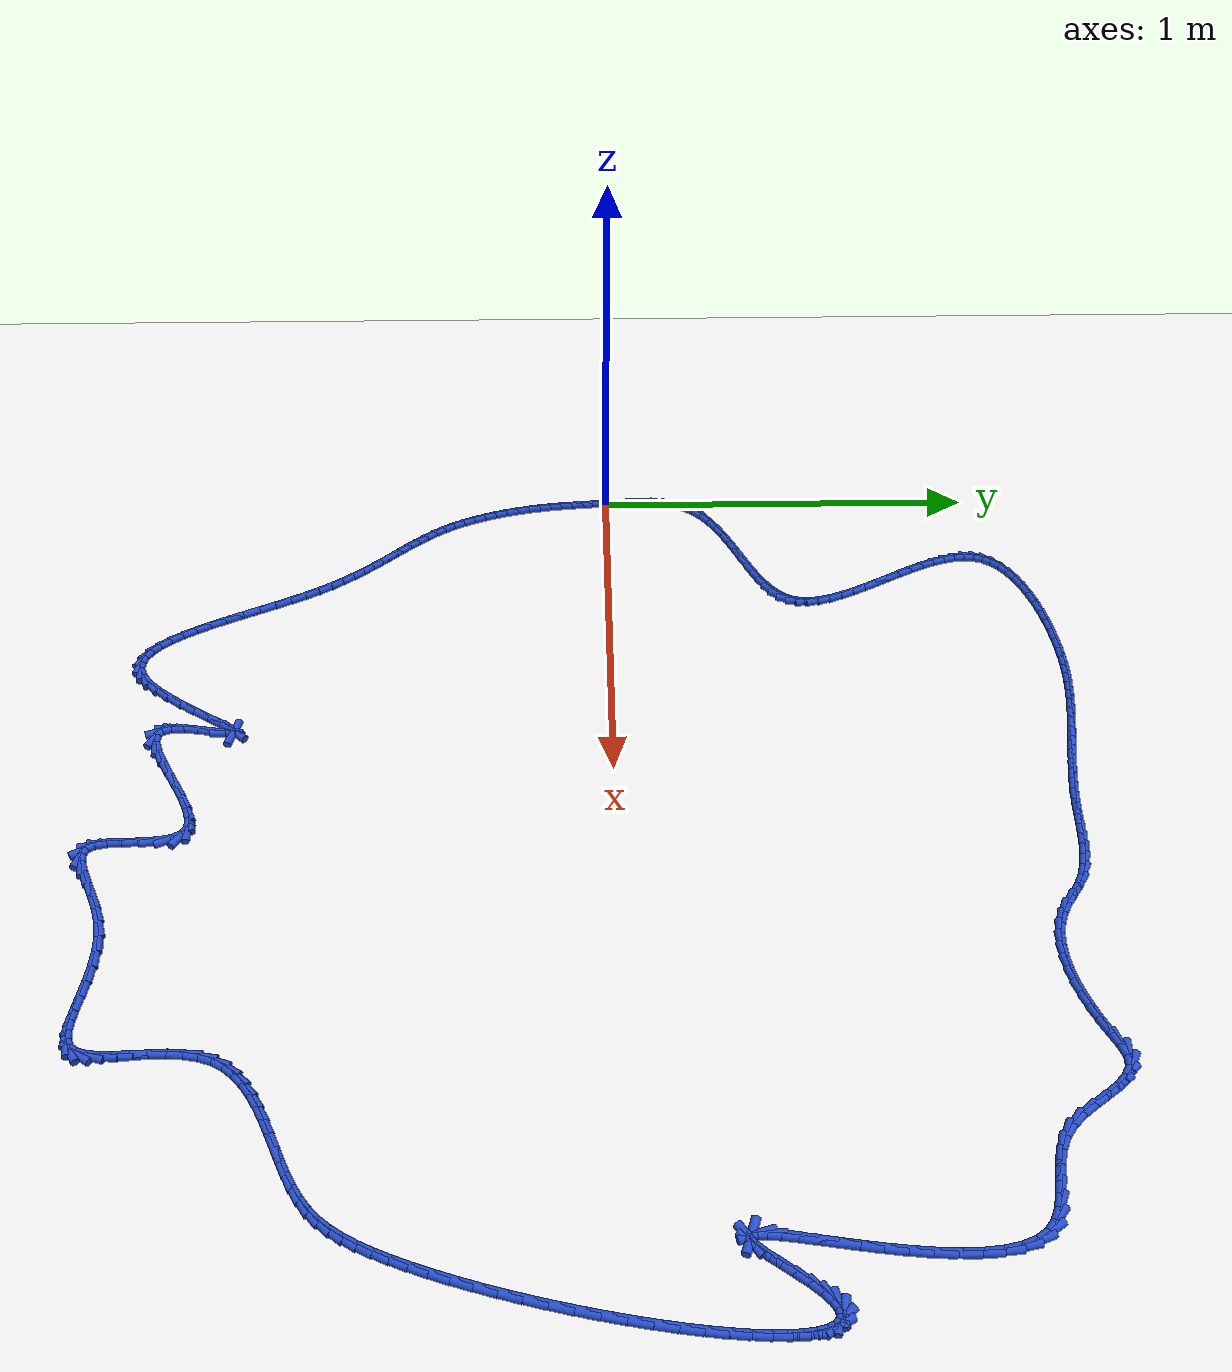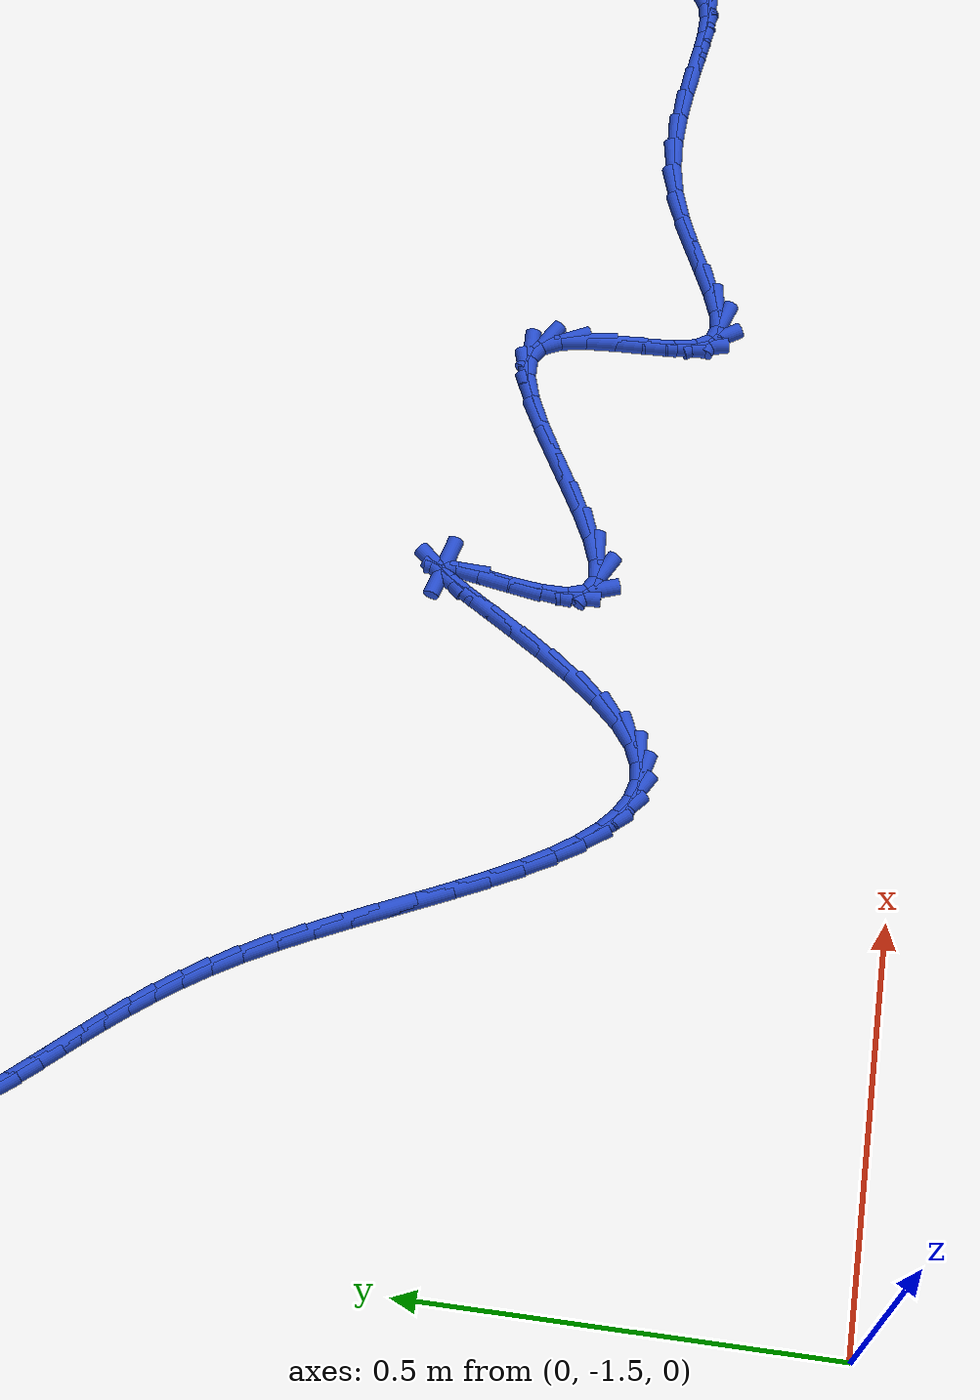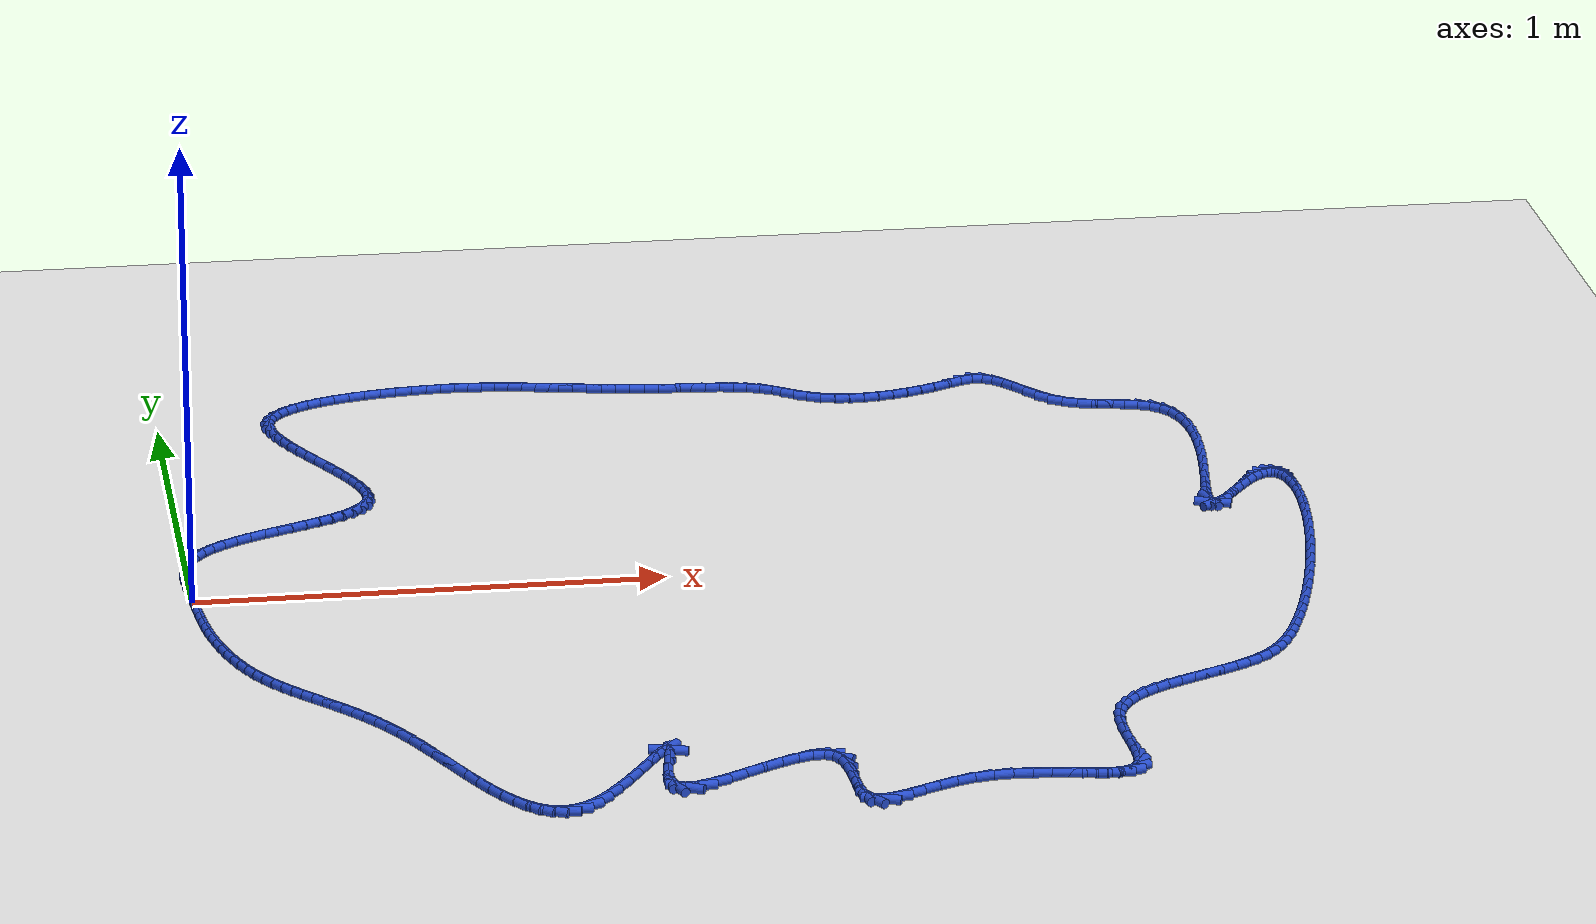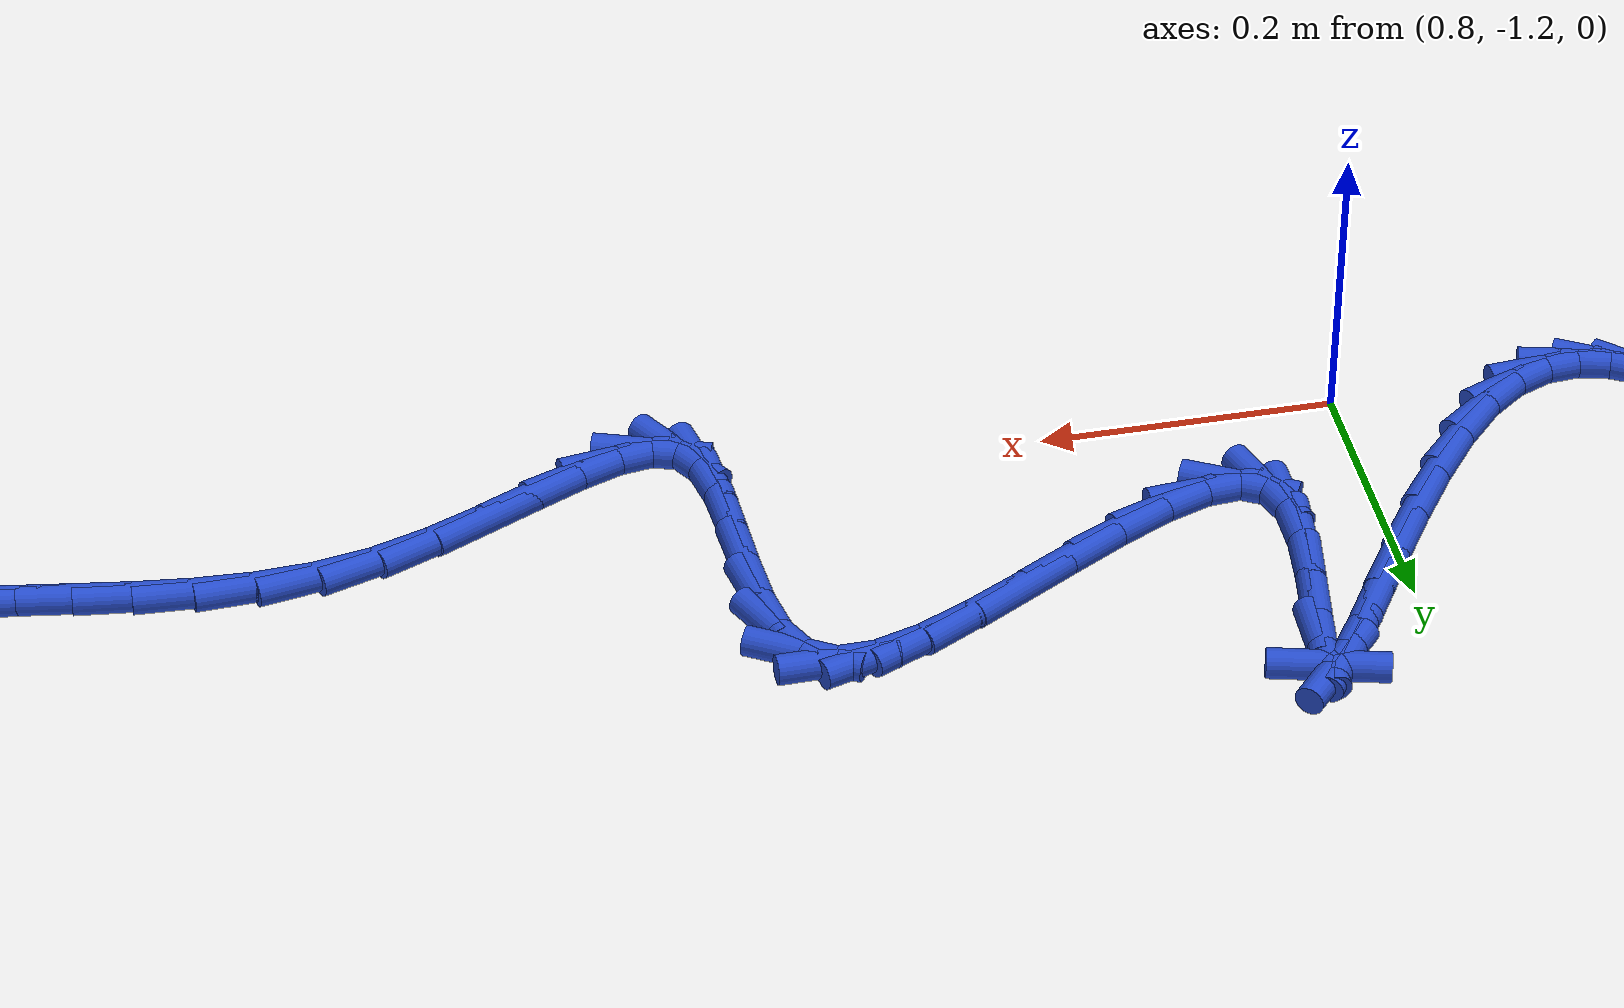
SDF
<sdf version="1.6">
 <world name="default">
  <light name="sun" type="directional">
   <pose>0 0 10 0 -0 0</pose>
   <diffuse>0.8 0.8 0.8 1</diffuse>
   <specular>0.2 0.2 0.2 1</specular>
   <attenuation>
    <range>1000</range>
    <constant>0.9</constant>
    <linear>0.01</linear>
    <quadratic>0.001</quadratic>
   </attenuation>
   <direction>-0.5 0.1 -0.9</direction>
  </light>
  <model name="ground_plane">
   <static>1</static>
   <link name="link">
    <collision name="collision">
     <geometry><plane><normal>0 0 1</normal><size>100 100</size></plane></geometry>
     <surface><friction><ode><mu>100</mu><mu2>50</mu2></ode></friction></surface>
    </collision>
    <visual name="visual">
     <cast_shadows>0</cast_shadows>
     <geometry><plane><normal>0 0 1</normal><size>100 100</size></plane></geometry>
     <material>
      <script><uri>file://media/materials/scripts/gazebo.material</uri><name>Gazebo/WhiteGlow</name></script>
     </material>
    </visual>
   </link>
  </model>
  <gravity>0 0 -9.8</gravity>
  <magnetic_field>6e-06 2.3e-05 -4.2e-05</magnetic_field>
  <atmosphere type="adiabatic"/>
  <physics name="default_physics" default="0" type="ode">
   <max_step_size>0.001</max_step_size>
   <real_time_factor>1</real_time_factor>
   <real_time_update_rate>1000</real_time_update_rate>
  </physics>
  <scene><ambient>0.4 0.4 0.4 1</ambient><background>0.7 0.7 0.7 1</background><shadows>1</shadows></scene>
  <spherical_coordinates>
   <surface_model>EARTH_WGS84</surface_model>
   <latitude_deg>0</latitude_deg>
   <longitude_deg>0</longitude_deg>
   <elevation>0</elevation>
   <heading_deg>0</heading_deg>
  </spherical_coordinates>
  <model name="line">
   <link name="link_0">
    <pose>2.8189256484623115e-17 1.3877787807814457e-17 0.01 0 1.57 -1.5020632470891158</pose>
    <collision name="collision">
     <geometry><cylinder><radius>0.01</radius><length>0.08</length></cylinder></geometry>
    </collision>
    <visual name="visual">
     <material>
      <script><name>Gazebo/Blue</name><uri>file://media/materials/scripts/gazebo.material</uri></script>
     </material>
     <geometry><cylinder><radius>0.01</radius><length>0.08</length></cylinder></geometry>
    </visual>
   </link>
   <link name="link_1">
    <pose>-0.002258916926638522 0.032813291596592624 0.01 0 1.57 -1.5216071057443248</pose>
    <collision name="collision">
     <geometry><cylinder><radius>0.01</radius><length>0.08</length></cylinder></geometry>
    </collision>
    <visual name="visual">
     <material>
      <script><name>Gazebo/Blue</name><uri>file://media/materials/scripts/gazebo.material</uri></script>
     </material>
     <geometry><cylinder><radius>0.01</radius><length>0.08</length></cylinder></geometry>
    </visual>
   </link>
   <link name="link_2">
    <pose>-0.0038874369943561913 0.06589384006792409 0.01 0 1.57 -1.5622753820476794</pose>
    <collision name="collision">
     <geometry><cylinder><radius>0.01</radius><length>0.08</length></cylinder></geometry>
    </collision>
    <visual name="visual">
     <material>
      <script><name>Gazebo/Blue</name><uri>file://media/materials/scripts/gazebo.material</uri></script>
     </material>
     <geometry><cylinder><radius>0.01</radius><length>0.08</length></cylinder></geometry>
    </visual>
   </link>
   <link name="link_3">
    <pose>-0.004167445133524468 0.09875420598255086 0.01 0 1.57 1.5152868049445425</pose>
    <collision name="collision">
     <geometry><cylinder><radius>0.01</radius><length>0.08</length></cylinder></geometry>
    </collision>
    <visual name="visual">
     <material>
      <script><name>Gazebo/Blue</name><uri>file://media/materials/scripts/gazebo.material</uri></script>
     </material>
     <geometry><cylinder><radius>0.01</radius><length>0.08</length></cylinder></geometry>
    </visual>
   </link>
   <link name="link_4">
    <pose>-0.002380826274514836 0.13090694990902918 0.01 0 1.57 1.4241909426000947</pose>
    <collision name="collision">
     <geometry><cylinder><radius>0.01</radius><length>0.08</length></cylinder></geometry>
    </collision>
    <visual name="visual">
     <material>
      <script><name>Gazebo/Blue</name><uri>file://media/materials/scripts/gazebo.material</uri></script>
     </material>
     <geometry><cylinder><radius>0.01</radius><length>0.08</length></cylinder></geometry>
    </visual>
   </link>
   <link name="link_5">
    <pose>0.0021905346523012105 0.16186463241591556 0.01 0 1.57 1.301682611133771</pose>
    <collision name="collision">
     <geometry><cylinder><radius>0.01</radius><length>0.08</length></cylinder></geometry>
    </collision>
    <visual name="visual">
     <material>
      <script><name>Gazebo/Blue</name><uri>file://media/materials/scripts/gazebo.material</uri></script>
     </material>
     <geometry><cylinder><radius>0.01</radius><length>0.08</length></cylinder></geometry>
    </visual>
   </link>
   <link name="link_6">
    <pose>0.010264752716552202 0.19113981407176636 0.01 0 1.57 1.1449449397419291</pose>
    <collision name="collision">
     <geometry><cylinder><radius>0.01</radius><length>0.08</length></cylinder></geometry>
    </collision>
    <visual name="visual">
     <material>
      <script><name>Gazebo/Blue</name><uri>file://media/materials/scripts/gazebo.material</uri></script>
     </material>
     <geometry><cylinder><radius>0.01</radius><length>0.08</length></cylinder></geometry>
    </visual>
   </link>
   <link name="link_7">
    <pose>0.022559942987866632 0.21824505544513784 0.01 0 1.57 0.9621370964178155</pose>
    <collision name="collision">
     <geometry><cylinder><radius>0.01</radius><length>0.08</length></cylinder></geometry>
    </collision>
    <visual name="visual">
     <material>
      <script><name>Gazebo/Blue</name><uri>file://media/materials/scripts/gazebo.material</uri></script>
     </material>
     <geometry><cylinder><radius>0.01</radius><length>0.08</length></cylinder></geometry>
    </visual>
   </link>
   <link name="link_8">
    <pose>0.039653928674670505 0.24277278142348785 0.01 0 1.57 0.7976940992005873</pose>
    <collision name="collision">
     <geometry><cylinder><radius>0.01</radius><length>0.08</length></cylinder></geometry>
    </collision>
    <visual name="visual">
     <material>
      <script><name>Gazebo/Blue</name><uri>file://media/materials/scripts/gazebo.material</uri></script>
     </material>
     <geometry><cylinder><radius>0.01</radius><length>0.08</length></cylinder></geometry>
    </visual>
   </link>
   <link name="link_9">
    <pose>0.06119146496127196 0.2648465869963455 0.01 0 1.57 0.66901977606405</pose>
    <collision name="collision">
     <geometry><cylinder><radius>0.01</radius><length>0.08</length></cylinder></geometry>
    </collision>
    <visual name="visual">
     <material>
      <script><name>Gazebo/Blue</name><uri>file://media/materials/scripts/gazebo.material</uri></script>
     </material>
     <geometry><cylinder><radius>0.01</radius><length>0.08</length></cylinder></geometry>
    </visual>
   </link>
   <link name="link_10">
    <pose>0.08643651870270493 0.2848068395326385 0.01 0 1.57 0.5725710399899394</pose>
    <collision name="collision">
     <geometry><cylinder><radius>0.01</radius><length>0.08</length></cylinder></geometry>
    </collision>
    <visual name="visual">
     <material>
      <script><name>Gazebo/Blue</name><uri>file://media/materials/scripts/gazebo.material</uri></script>
     </material>
     <geometry><cylinder><radius>0.01</radius><length>0.08</length></cylinder></geometry>
    </visual>
   </link>
   <link name="link_11">
    <pose>0.11465193104637088 0.3029945472358558 0.01 0 1.57 0.5030810664577722</pose>
    <collision name="collision">
     <geometry><cylinder><radius>0.01</radius><length>0.08</length></cylinder></geometry>
    </collision>
    <visual name="visual">
     <material>
      <script><name>Gazebo/Blue</name><uri>file://media/materials/scripts/gazebo.material</uri></script>
     </material>
     <geometry><cylinder><radius>0.01</radius><length>0.08</length></cylinder></geometry>
    </visual>
   </link>
   <link name="link_12">
    <pose>0.14510054313967136 0.319750718309486 0.01 0 1.57 0.45593777381615547</pose>
    <collision name="collision">
     <geometry><cylinder><radius>0.01</radius><length>0.08</length></cylinder></geometry>
    </collision>
    <visual name="visual">
     <material>
      <script><name>Gazebo/Blue</name><uri>file://media/materials/scripts/gazebo.material</uri></script>
     </material>
     <geometry><cylinder><radius>0.01</radius><length>0.08</length></cylinder></geometry>
    </visual>
   </link>
   <link name="link_13">
    <pose>0.17704519613000783 0.3354163609570181 0.01 0 1.57 0.42791610944207825</pose>
    <collision name="collision">
     <geometry><cylinder><radius>0.01</radius><length>0.08</length></cylinder></geometry>
    </collision>
    <visual name="visual">
     <material>
      <script><name>Gazebo/Blue</name><uri>file://media/materials/scripts/gazebo.material</uri></script>
     </material>
     <geometry><cylinder><radius>0.01</radius><length>0.08</length></cylinder></geometry>
    </visual>
   </link>
   <link name="link_14">
    <pose>0.20974873116478177 0.350332483381941 0.01 0 1.57 0.41728111065739104</pose>
    <collision name="collision">
     <geometry><cylinder><radius>0.01</radius><length>0.08</length></cylinder></geometry>
    </collision>
    <visual name="visual">
     <material>
      <script><name>Gazebo/Blue</name><uri>file://media/materials/scripts/gazebo.material</uri></script>
     </material>
     <geometry><cylinder><radius>0.01</radius><length>0.08</length></cylinder></geometry>
    </visual>
   </link>
   <link name="link_15">
    <pose>0.24247398939139475 0.36484009378774346 0.01 0 1.57 0.423780656820157</pose>
    <collision name="collision">
     <geometry><cylinder><radius>0.01</radius><length>0.08</length></cylinder></geometry>
    </collision>
    <visual name="visual">
     <material>
      <script><name>Gazebo/Blue</name><uri>file://media/materials/scripts/gazebo.material</uri></script>
     </material>
     <geometry><cylinder><radius>0.01</radius><length>0.08</length></cylinder></geometry>
    </visual>
   </link>
   <link name="link_16">
    <pose>0.27448381195724836 0.3792802003779146 0.01 0 1.57 0.4487464978163053</pose>
    <collision name="collision">
     <geometry><cylinder><radius>0.01</radius><length>0.08</length></cylinder></geometry>
    </collision>
    <visual name="visual">
     <material>
      <script><name>Gazebo/Blue</name><uri>file://media/materials/scripts/gazebo.material</uri></script>
     </material>
     <geometry><cylinder><radius>0.01</radius><length>0.08</length></cylinder></geometry>
    </visual>
   </link>
   <link name="link_17">
    <pose>0.3050410400097441 0.39399381135594297 0.01 0 1.57 0.4953976195313095</pose>
    <collision name="collision">
     <geometry><cylinder><radius>0.01</radius><length>0.08</length></cylinder></geometry>
    </collision>
    <visual name="visual">
     <material>
      <script><name>Gazebo/Blue</name><uri>file://media/materials/scripts/gazebo.material</uri></script>
     </material>
     <geometry><cylinder><radius>0.01</radius><length>0.08</length></cylinder></geometry>
    </visual>
   </link>
   <link name="link_18">
    <pose>0.3334085146962832 0.40932193492531765 0.01 0 1.57 0.5693601594862281</pose>
    <collision name="collision">
     <geometry><cylinder><radius>0.01</radius><length>0.08</length></cylinder></geometry>
    </collision>
    <visual name="visual">
     <material>
      <script><name>Gazebo/Blue</name><uri>file://media/materials/scripts/gazebo.material</uri></script>
     </material>
     <geometry><cylinder><radius>0.01</radius><length>0.08</length></cylinder></geometry>
    </visual>
   </link>
   <link name="link_19">
    <pose>0.35884907716426745 0.42560557928952747 0.01 0 1.57 0.6791766678790981</pose>
    <collision name="collision">
     <geometry><cylinder><radius>0.01</radius><length>0.08</length></cylinder></geometry>
    </collision>
    <visual name="visual">
     <material>
      <script><name>Gazebo/Blue</name><uri>file://media/materials/scripts/gazebo.material</uri></script>
     </material>
     <geometry><cylinder><radius>0.01</radius><length>0.08</length></cylinder></geometry>
    </visual>
   </link>
   <link name="link_20">
    <pose>0.38062556856109836 0.4431857526520613 0.01 0 1.57 0.835705487997839</pose>
    <collision name="collision">
     <geometry><cylinder><radius>0.01</radius><length>0.08</length></cylinder></geometry>
    </collision>
    <visual name="visual">
     <material>
      <script><name>Gazebo/Blue</name><uri>file://media/materials/scripts/gazebo.material</uri></script>
     </material>
     <geometry><cylinder><radius>0.01</radius><length>0.08</length></cylinder></geometry>
    </visual>
   </link>
   <link name="link_21">
    <pose>0.39800083003417747 0.462403463216408 0.01 0 1.57 1.0472255539942117</pose>
    <collision name="collision">
     <geometry><cylinder><radius>0.01</radius><length>0.08</length></cylinder></geometry>
    </collision>
    <visual name="visual">
     <material>
      <script><name>Gazebo/Blue</name><uri>file://media/materials/scripts/gazebo.material</uri></script>
     </material>
     <geometry><cylinder><radius>0.01</radius><length>0.08</length></cylinder></geometry>
    </visual>
   </link>
   <link name="link_22">
    <pose>0.410237702730906 0.48359971918605643 0.01 0 1.57 1.3004957251476283</pose>
    <collision name="collision">
     <geometry><cylinder><radius>0.01</radius><length>0.08</length></cylinder></geometry>
    </collision>
    <visual name="visual">
     <material>
      <script><name>Gazebo/Blue</name><uri>file://media/materials/scripts/gazebo.material</uri></script>
     </material>
     <geometry><cylinder><radius>0.01</radius><length>0.08</length></cylinder></geometry>
    </visual>
   </link>
   <link name="link_23">
    <pose>0.4167371741477261 0.5070565888664732 0.01 0 1.57 1.5288175513280917</pose>
    <collision name="collision">
     <geometry><cylinder><radius>0.01</radius><length>0.08</length></cylinder></geometry>
    </collision>
    <visual name="visual">
     <material>
      <script><name>Gazebo/Blue</name><uri>file://media/materials/scripts/gazebo.material</uri></script>
     </material>
     <geometry><cylinder><radius>0.01</radius><length>0.08</length></cylinder></geometry>
    </visual>
   </link>
   <link name="link_24">
    <pose>0.4178128895889665 0.5326667567068034 0.01 0 1.57 -1.4383247169666176</pose>
    <collision name="collision">
     <geometry><cylinder><radius>0.01</radius><length>0.08</length></cylinder></geometry>
    </collision>
    <visual name="visual">
     <material>
      <script><name>Gazebo/Blue</name><uri>file://media/materials/scripts/gazebo.material</uri></script>
     </material>
     <geometry><cylinder><radius>0.01</radius><length>0.08</length></cylinder></geometry>
    </visual>
   </link>
   <link name="link_25">
    <pose>0.4141486992704831 0.5601649598786541 0.01 0 1.57 -1.3116784470120486</pose>
    <collision name="collision">
     <geometry><cylinder><radius>0.01</radius><length>0.08</length></cylinder></geometry>
    </collision>
    <visual name="visual">
     <material>
      <script><name>Gazebo/Blue</name><uri>file://media/materials/scripts/gazebo.material</uri></script>
     </material>
     <geometry><cylinder><radius>0.01</radius><length>0.08</length></cylinder></geometry>
    </visual>
   </link>
   <link name="link_26">
    <pose>0.40642951176340913 0.5892854840082056 0.01 0 1.57 -1.2218316629321162</pose>
    <collision name="collision">
     <geometry><cylinder><radius>0.01</radius><length>0.08</length></cylinder></geometry>
    </collision>
    <visual name="visual">
     <material>
      <script><name>Gazebo/Blue</name><uri>file://media/materials/scripts/gazebo.material</uri></script>
     </material>
     <geometry><cylinder><radius>0.01</radius><length>0.08</length></cylinder></geometry>
    </visual>
   </link>
   <link name="link_27">
    <pose>0.39534023563887816 0.6197626147216379 0.01 0 1.57 -1.159358208141954</pose>
    <collision name="collision">
     <geometry><cylinder><radius>0.01</radius><length>0.08</length></cylinder></geometry>
    </collision>
    <visual name="visual">
     <material>
      <script><name>Gazebo/Blue</name><uri>file://media/materials/scripts/gazebo.material</uri></script>
     </material>
     <geometry><cylinder><radius>0.01</radius><length>0.08</length></cylinder></geometry>
    </visual>
   </link>
   <link name="link_28">
    <pose>0.3815657794680231 0.6513306376451315 0.01 0 1.57 -1.1176216918937338</pose>
    <collision name="collision">
     <geometry><cylinder><radius>0.01</radius><length>0.08</length></cylinder></geometry>
    </collision>
    <visual name="visual">
     <material>
      <script><name>Gazebo/Blue</name><uri>file://media/materials/scripts/gazebo.material</uri></script>
     </material>
     <geometry><cylinder><radius>0.01</radius><length>0.08</length></cylinder></geometry>
    </visual>
   </link>
   <link name="link_29">
    <pose>0.36579105182197763 0.6837238384048671 0.01 0 1.57 -1.0923596198112473</pose>
    <collision name="collision">
     <geometry><cylinder><radius>0.01</radius><length>0.08</length></cylinder></geometry>
    </collision>
    <visual name="visual">
     <material>
      <script><name>Gazebo/Blue</name><uri>file://media/materials/scripts/gazebo.material</uri></script>
     </material>
     <geometry><cylinder><radius>0.01</radius><length>0.08</length></cylinder></geometry>
    </visual>
   </link>
   <link name="link_30">
    <pose>0.3487009612718749 0.7166765026270242 0.01 0 1.57 -1.0810937129273226</pose>
    <collision name="collision">
     <geometry><cylinder><radius>0.01</radius><length>0.08</length></cylinder></geometry>
    </collision>
    <visual name="visual">
     <material>
      <script><name>Gazebo/Blue</name><uri>file://media/materials/scripts/gazebo.material</uri></script>
     </material>
     <geometry><cylinder><radius>0.01</radius><length>0.08</length></cylinder></geometry>
    </visual>
   </link>
   <link name="link_31">
    <pose>0.3309804163888484 0.7499229159377837 0.01 0 1.57 -1.0827192904570244</pose>
    <collision name="collision">
     <geometry><cylinder><radius>0.01</radius><length>0.08</length></cylinder></geometry>
    </collision>
    <visual name="visual">
     <material>
      <script><name>Gazebo/Blue</name><uri>file://media/materials/scripts/gazebo.material</uri></script>
     </material>
     <geometry><cylinder><radius>0.01</radius><length>0.08</length></cylinder></geometry>
    </visual>
   </link>
   <link name="link_32">
    <pose>0.3133143257440314 0.783197363963326 0.01 0 1.57 -1.0973094606091522</pose>
    <collision name="collision">
     <geometry><cylinder><radius>0.01</radius><length>0.08</length></cylinder></geometry>
    </collision>
    <visual name="visual">
     <material>
      <script><name>Gazebo/Blue</name><uri>file://media/materials/scripts/gazebo.material</uri></script>
     </material>
     <geometry><cylinder><radius>0.01</radius><length>0.08</length></cylinder></geometry>
    </visual>
   </link>
   <link name="link_33">
    <pose>0.29638759790855707 0.8162341323298307 0.01 0 1.57 -1.1261172318951667</pose>
    <collision name="collision">
     <geometry><cylinder><radius>0.01</radius><length>0.08</length></cylinder></geometry>
    </collision>
    <visual name="visual">
     <material>
      <script><name>Gazebo/Blue</name><uri>file://media/materials/scripts/gazebo.material</uri></script>
     </material>
     <geometry><cylinder><radius>0.01</radius><length>0.08</length></cylinder></geometry>
    </visual>
   </link>
   <link name="link_34">
    <pose>0.280885141453559 0.8487675066634789 0.01 0 1.57 -1.171769951742503</pose>
    <collision name="collision">
     <geometry><cylinder><radius>0.01</radius><length>0.08</length></cylinder></geometry>
    </collision>
    <visual name="visual">
     <material>
      <script><name>Gazebo/Blue</name><uri>file://media/materials/scripts/gazebo.material</uri></script>
     </material>
     <geometry><cylinder><radius>0.01</radius><length>0.08</length></cylinder></geometry>
    </visual>
   </link>
   <link name="link_35">
    <pose>0.26749186495017024 0.8805317725904501 0.01 0 1.57 -1.2386546045010396</pose>
    <collision name="collision">
     <geometry><cylinder><radius>0.01</radius><length>0.08</length></cylinder></geometry>
    </collision>
    <visual name="visual">
     <material>
      <script><name>Gazebo/Blue</name><uri>file://media/materials/scripts/gazebo.material</uri></script>
     </material>
     <geometry><cylinder><radius>0.01</radius><length>0.08</length></cylinder></geometry>
    </visual>
   </link>
   <link name="link_36">
    <pose>0.25689267696952445 0.9112612157369254 0.01 0 1.57 -1.3334126332315617</pose>
    <collision name="collision">
     <geometry><cylinder><radius>0.01</radius><length>0.08</length></cylinder></geometry>
    </collision>
    <visual name="visual">
     <material>
      <script><name>Gazebo/Blue</name><uri>file://media/materials/scripts/gazebo.material</uri></script>
     </material>
     <geometry><cylinder><radius>0.01</radius><length>0.08</length></cylinder></geometry>
    </visual>
   </link>
   <link name="link_37">
    <pose>0.24977248608275465 0.9406901217290846 0.01 0 1.57 -1.4650897454526481</pose>
    <collision name="collision">
     <geometry><cylinder><radius>0.01</radius><length>0.08</length></cylinder></geometry>
    </collision>
    <visual name="visual">
     <material>
      <script><name>Gazebo/Blue</name><uri>file://media/materials/scripts/gazebo.material</uri></script>
     </material>
     <geometry><cylinder><radius>0.01</radius><length>0.08</length></cylinder></geometry>
    </visual>
   </link>
   <link name="link_38">
    <pose>0.24681620086099437 0.9685527761931083 0.01 0 1.57 1.4982202590435205</pose>
    <collision name="collision">
     <geometry><cylinder><radius>0.01</radius><length>0.08</length></cylinder></geometry>
    </collision>
    <visual name="visual">
     <material>
      <script><name>Gazebo/Blue</name><uri>file://media/materials/scripts/gazebo.material</uri></script>
     </material>
     <geometry><cylinder><radius>0.01</radius><length>0.08</length></cylinder></geometry>
    </visual>
   </link>
   <link name="link_39">
    <pose>0.24870872987537687 0.9945834647551766 0.01 0 1.57 1.270220806164153</pose>
    <collision name="collision">
     <geometry><cylinder><radius>0.01</radius><length>0.08</length></cylinder></geometry>
    </collision>
    <visual name="visual">
     <material>
      <script><name>Gazebo/Blue</name><uri>file://media/materials/scripts/gazebo.material</uri></script>
     </material>
     <geometry><cylinder><radius>0.01</radius><length>0.08</length></cylinder></geometry>
    </visual>
   </link>
   <link name="link_40">
    <pose>0.2561277604412661 1.0185183729161589 0.01 0 1.57 1.0262948243847396</pose>
    <collision name="collision">
     <geometry><cylinder><radius>0.01</radius><length>0.08</length></cylinder></geometry>
    </collision>
    <visual name="visual">
     <material>
      <script><name>Gazebo/Blue</name><uri>file://media/materials/scripts/gazebo.material</uri></script>
     </material>
     <geometry><cylinder><radius>0.01</radius><length>0.08</length></cylinder></geometry>
    </visual>
   </link>
   <link name="link_41">
    <pose>0.2692696974094262 1.0402203090804834 0.01 0 1.57 0.8184200096045168</pose>
    <collision name="collision">
     <geometry><cylinder><radius>0.01</radius><length>0.08</length></cylinder></geometry>
    </collision>
    <visual name="visual">
     <material>
      <script><name>Gazebo/Blue</name><uri>file://media/materials/scripts/gazebo.material</uri></script>
     </material>
     <geometry><cylinder><radius>0.01</radius><length>0.08</length></cylinder></geometry>
    </visual>
   </link>
   <link name="link_42">
    <pose>0.28755596041702075 1.059755976215914 0.01 0 1.57 0.6537644450391985</pose>
    <collision name="collision">
     <geometry><cylinder><radius>0.01</radius><length>0.08</length></cylinder></geometry>
    </collision>
    <visual name="visual">
     <material>
      <script><name>Gazebo/Blue</name><uri>file://media/materials/scripts/gazebo.material</uri></script>
     </material>
     <geometry><cylinder><radius>0.01</radius><length>0.08</length></cylinder></geometry>
    </visual>
   </link>
   <link name="link_43">
    <pose>0.31033779546940155 1.0772105396063525 0.01 0 1.57 0.5259772832186632</pose>
    <collision name="collision">
     <geometry><cylinder><radius>0.01</radius><length>0.08</length></cylinder></geometry>
    </collision>
    <visual name="visual">
     <material>
      <script><name>Gazebo/Blue</name><uri>file://media/materials/scripts/gazebo.material</uri></script>
     </material>
     <geometry><cylinder><radius>0.01</radius><length>0.08</length></cylinder></geometry>
    </visual>
   </link>
   <link name="link_44">
    <pose>0.3369664485719204 1.092669164535702 0.01 0 1.57 0.42635663022842796</pose>
    <collision name="collision">
     <geometry><cylinder><radius>0.01</radius><length>0.08</length></cylinder></geometry>
    </collision>
    <visual name="visual">
     <material>
      <script><name>Gazebo/Blue</name><uri>file://media/materials/scripts/gazebo.material</uri></script>
     </material>
     <geometry><cylinder><radius>0.01</radius><length>0.08</length></cylinder></geometry>
    </visual>
   </link>
   <link name="link_45">
    <pose>0.3667931657299286 1.1062170162878644 0.01 0 1.57 0.34738293662290737</pose>
    <collision name="collision">
     <geometry><cylinder><radius>0.01</radius><length>0.08</length></cylinder></geometry>
    </collision>
    <visual name="visual">
     <material>
      <script><name>Gazebo/Blue</name><uri>file://media/materials/scripts/gazebo.material</uri></script>
     </material>
     <geometry><cylinder><radius>0.01</radius><length>0.08</length></cylinder></geometry>
    </visual>
   </link>
   <link name="link_46">
    <pose>0.3991691929487781 1.117939260146742 0.01 0 1.57 0.2833763517244959</pose>
    <collision name="collision">
     <geometry><cylinder><radius>0.01</radius><length>0.08</length></cylinder></geometry>
    </collision>
    <visual name="visual">
     <material>
      <script><name>Gazebo/Blue</name><uri>file://media/materials/scripts/gazebo.material</uri></script>
     </material>
     <geometry><cylinder><radius>0.01</radius><length>0.08</length></cylinder></geometry>
    </visual>
   </link>
   <link name="link_47">
    <pose>0.4334457762338202 1.1279210613962372 0.01 0 1.57 0.23020781046405236</pose>
    <collision name="collision">
     <geometry><cylinder><radius>0.01</radius><length>0.08</length></cylinder></geometry>
    </collision>
    <visual name="visual">
     <material>
      <script><name>Gazebo/Blue</name><uri>file://media/materials/scripts/gazebo.material</uri></script>
     </material>
     <geometry><cylinder><radius>0.01</radius><length>0.08</length></cylinder></geometry>
    </visual>
   </link>
   <link name="link_48">
    <pose>0.468974161590407 1.1362475853202518 0.01 0 1.57 0.18486044377016012</pose>
    <collision name="collision">
     <geometry><cylinder><radius>0.01</radius><length>0.08</length></cylinder></geometry>
    </collision>
    <visual name="visual">
     <material>
      <script><name>Gazebo/Blue</name><uri>file://media/materials/scripts/gazebo.material</uri></script>
     </material>
     <geometry><cylinder><radius>0.01</radius><length>0.08</length></cylinder></geometry>
    </visual>
   </link>
   <link name="link_49">
    <pose>0.5051055950238896 1.1430039972026889 0.01 0 1.57 0.14505570325811318</pose>
    <collision name="collision">
     <geometry><cylinder><radius>0.01</radius><length>0.08</length></cylinder></geometry>
    </collision>
    <visual name="visual">
     <material>
      <script><name>Gazebo/Blue</name><uri>file://media/materials/scripts/gazebo.material</uri></script>
     </material>
     <geometry><cylinder><radius>0.01</radius><length>0.08</length></cylinder></geometry>
    </visual>
   </link>
   <link name="link_50">
    <pose>0.5411913225396201 1.1482754623274503 0.01 0 1.57 0.10896328220465569</pose>
    <collision name="collision">
     <geometry><cylinder><radius>0.01</radius><length>0.08</length></cylinder></geometry>
    </collision>
    <visual name="visual">
     <material>
      <script><name>Gazebo/Blue</name><uri>file://media/materials/scripts/gazebo.material</uri></script>
     </material>
     <geometry><cylinder><radius>0.01</radius><length>0.08</length></cylinder></geometry>
    </visual>
   </link>
   <link name="link_51">
    <pose>0.5765825901429498 1.1521471459784385 0.01 0 1.57 0.07490406522854538</pose>
    <collision name="collision">
     <geometry><cylinder><radius>0.01</radius><length>0.08</length></cylinder></geometry>
    </collision>
    <visual name="visual">
     <material>
      <script><name>Gazebo/Blue</name><uri>file://media/materials/scripts/gazebo.material</uri></script>
     </material>
     <geometry><cylinder><radius>0.01</radius><length>0.08</length></cylinder></geometry>
    </visual>
   </link>
   <link name="link_52">
    <pose>0.6106499395034645 1.1547037120324795 0.01 0 1.57 0.04030807978802277</pose>
    <collision name="collision">
     <geometry><cylinder><radius>0.01</radius><length>0.08</length></cylinder></geometry>
    </collision>
    <visual name="visual">
     <material>
      <script><name>Gazebo/Blue</name><uri>file://media/materials/scripts/gazebo.material</uri></script>
     </material>
     <geometry><cylinder><radius>0.01</radius><length>0.08</length></cylinder></geometry>
    </visual>
   </link>
   <link name="link_53">
    <pose>0.6432307457716007 1.1560176934748234 0.01 0 1.57 0.004184946276572827</pose>
    <collision name="collision">
     <geometry><cylinder><radius>0.01</radius><length>0.08</length></cylinder></geometry>
    </collision>
    <visual name="visual">
     <material>
      <script><name>Gazebo/Blue</name><uri>file://media/materials/scripts/gazebo.material</uri></script>
     </material>
     <geometry><cylinder><radius>0.01</radius><length>0.08</length></cylinder></geometry>
    </visual>
   </link>
   <link name="link_54">
    <pose>0.6746423840887169 1.1561491502610755 0.01 0 1.57 -0.03241245800114558</pose>
    <collision name="collision">
     <geometry><cylinder><radius>0.01</radius><length>0.08</length></cylinder></geometry>
    </collision>
    <visual name="visual">
     <material>
      <script><name>Gazebo/Blue</name><uri>file://media/materials/scripts/gazebo.material</uri></script>
     </material>
     <geometry><cylinder><radius>0.01</radius><length>0.08</length></cylinder></geometry>
    </visual>
   </link>
   <link name="link_55">
    <pose>0.7052241592010271 1.1551575724955554 0.01 0 1.57 -0.06819052367357738</pose>
    <collision name="collision">
     <geometry><cylinder><radius>0.01</radius><length>0.08</length></cylinder></geometry>
    </collision>
    <visual name="visual">
     <material>
      <script><name>Gazebo/Blue</name><uri>file://media/materials/scripts/gazebo.material</uri></script>
     </material>
     <geometry><cylinder><radius>0.01</radius><length>0.08</length></cylinder></geometry>
    </visual>
   </link>
   <link name="link_56">
    <pose>0.7353153758547443 1.1531024502825835 0.01 0 1.57 -0.10181067429609024</pose>
    <collision name="collision">
     <geometry><cylinder><radius>0.01</radius><length>0.08</length></cylinder></geometry>
    </collision>
    <visual name="visual">
     <material>
      <script><name>Gazebo/Blue</name><uri>file://media/materials/scripts/gazebo.material</uri></script>
     </material>
     <geometry><cylinder><radius>0.01</radius><length>0.08</length></cylinder></geometry>
    </visual>
   </link>
   <link name="link_57">
    <pose>0.7652534905579499 1.1500438554610093 0.01 0 1.57 -0.13138188576686016</pose>
    <collision name="collision">
     <geometry><cylinder><radius>0.01</radius><length>0.08</length></cylinder></geometry>
    </collision>
    <visual name="visual">
     <material>
      <script><name>Gazebo/Blue</name><uri>file://media/materials/scripts/gazebo.material</uri></script>
     </material>
     <geometry><cylinder><radius>0.01</radius><length>0.08</length></cylinder></geometry>
    </visual>
   </link>
   <link name="link_58">
    <pose>0.7952581128041347 1.1460789523181196 0.01 0 1.57 -0.15537010714341098</pose>
    <collision name="collision">
     <geometry><cylinder><radius>0.01</radius><length>0.08</length></cylinder></geometry>
    </collision>
    <visual name="visual">
     <material>
      <script><name>Gazebo/Blue</name><uri>file://media/materials/scripts/gazebo.material</uri></script>
     </material>
     <geometry><cylinder><radius>0.01</radius><length>0.08</length></cylinder></geometry>
    </visual>
   </link>
   <link name="link_59">
    <pose>0.8253620751071308 1.141363693354984 0.01 0 1.57 -0.1737601401998908</pose>
    <collision name="collision">
     <geometry><cylinder><radius>0.01</radius><length>0.08</length></cylinder></geometry>
    </collision>
    <visual name="visual">
     <material>
      <script><name>Gazebo/Blue</name><uri>file://media/materials/scripts/gazebo.material</uri></script>
     </material>
     <geometry><cylinder><radius>0.01</radius><length>0.08</length></cylinder></geometry>
    </visual>
   </link>
   <link name="link_60">
    <pose>0.85558165248856 1.136059242557477 0.01 0 1.57 -0.18667099659686182</pose>
    <collision name="collision">
     <geometry><cylinder><radius>0.01</radius><length>0.08</length></cylinder></geometry>
    </collision>
    <visual name="visual">
     <material>
      <script><name>Gazebo/Blue</name><uri>file://media/materials/scripts/gazebo.material</uri></script>
     </material>
     <geometry><cylinder><radius>0.01</radius><length>0.08</length></cylinder></geometry>
    </visual>
   </link>
   <link name="link_61">
    <pose>0.8859331199700451 1.1303267639114734 0.01 0 1.57 -0.19422252333711698</pose>
    <collision name="collision">
     <geometry><cylinder><radius>0.01</radius><length>0.08</length></cylinder></geometry>
    </collision>
    <visual name="visual">
     <material>
      <script><name>Gazebo/Blue</name><uri>file://media/materials/scripts/gazebo.material</uri></script>
     </material>
     <geometry><cylinder><radius>0.01</radius><length>0.08</length></cylinder></geometry>
    </visual>
   </link>
   <link name="link_62">
    <pose>0.9164327525732083 1.1243274214028485 0.01 0 1.57 -0.19652455197307178</pose>
    <collision name="collision">
     <geometry><cylinder><radius>0.01</radius><length>0.08</length></cylinder></geometry>
    </collision>
    <visual name="visual">
     <material>
      <script><name>Gazebo/Blue</name><uri>file://media/materials/scripts/gazebo.material</uri></script>
     </material>
     <geometry><cylinder><radius>0.01</radius><length>0.08</length></cylinder></geometry>
    </visual>
   </link>
   <link name="link_63">
    <pose>0.9470968253196723 1.1182223790174772 0.01 0 1.57 -0.19367134028679195</pose>
    <collision name="collision">
     <geometry><cylinder><radius>0.01</radius><length>0.08</length></cylinder></geometry>
    </collision>
    <visual name="visual">
     <material>
      <script><name>Gazebo/Blue</name><uri>file://media/materials/scripts/gazebo.material</uri></script>
     </material>
     <geometry><cylinder><radius>0.01</radius><length>0.08</length></cylinder></geometry>
    </visual>
   </link>
   <link name="link_64">
    <pose>0.9779416132310593 1.112172800741235 0.01 0 1.57 -0.1857405626639809</pose>
    <collision name="collision">
     <geometry><cylinder><radius>0.01</radius><length>0.08</length></cylinder></geometry>
    </collision>
    <visual name="visual">
     <material>
      <script><name>Gazebo/Blue</name><uri>file://media/materials/scripts/gazebo.material</uri></script>
     </material>
     <geometry><cylinder><radius>0.01</radius><length>0.08</length></cylinder></geometry>
    </visual>
   </link>
   <link name="link_65">
    <pose>1.0089833913289916 1.1063398505599968 0.01 0 1.57 -0.17279628384267373</pose>
    <collision name="collision">
     <geometry><cylinder><radius>0.01</radius><length>0.08</length></cylinder></geometry>
    </collision>
    <visual name="visual">
     <material>
      <script><name>Gazebo/Blue</name><uri>file://media/materials/scripts/gazebo.material</uri></script>
     </material>
     <geometry><cylinder><radius>0.01</radius><length>0.08</length></cylinder></geometry>
    </visual>
   </link>
   <link name="link_66">
    <pose>1.0402384346350921 1.1008846924596376 0.01 0 1.57 -0.15489553675946843</pose>
    <collision name="collision">
     <geometry><cylinder><radius>0.01</radius><length>0.08</length></cylinder></geometry>
    </collision>
    <visual name="visual">
     <material>
      <script><name>Gazebo/Blue</name><uri>file://media/materials/scripts/gazebo.material</uri></script>
     </material>
     <geometry><cylinder><radius>0.01</radius><length>0.08</length></cylinder></geometry>
    </visual>
   </link>
   <link name="link_67">
    <pose>1.0717230181709827 1.0959684904260327 0.01 0 1.57 -0.13209824324151964</pose>
    <collision name="collision">
     <geometry><cylinder><radius>0.01</radius><length>0.08</length></cylinder></geometry>
    </collision>
    <visual name="visual">
     <material>
      <script><name>Gazebo/Blue</name><uri>file://media/materials/scripts/gazebo.material</uri></script>
     </material>
     <geometry><cylinder><radius>0.01</radius><length>0.08</length></cylinder></geometry>
    </visual>
   </link>
   <link name="link_68">
    <pose>1.103453416958286 1.0917524084450565 0.01 0 1.57 -0.10448020860099032</pose>
    <collision name="collision">
     <geometry><cylinder><radius>0.01</radius><length>0.08</length></cylinder></geometry>
    </collision>
    <visual name="visual">
     <material>
      <script><name>Gazebo/Blue</name><uri>file://media/materials/scripts/gazebo.material</uri></script>
     </material>
     <geometry><cylinder><radius>0.01</radius><length>0.08</length></cylinder></geometry>
    </visual>
   </link>
   <link name="link_69">
    <pose>1.1354459060186242 1.0883976105025845 0.01 0 1.57 -0.0761364733005052</pose>
    <collision name="collision">
     <geometry><cylinder><radius>0.01</radius><length>0.08</length></cylinder></geometry>
    </collision>
    <visual name="visual">
     <material>
      <script><name>Gazebo/Blue</name><uri>file://media/materials/scripts/gazebo.material</uri></script>
     </material>
     <geometry><cylinder><radius>0.01</radius><length>0.08</length></cylinder></geometry>
    </visual>
   </link>
   <link name="link_70">
    <pose>1.167677235391699 1.0859388780211932 0.01 0 1.57 -0.06432021495907078</pose>
    <collision name="collision">
     <geometry><cylinder><radius>0.01</radius><length>0.08</length></cylinder></geometry>
    </collision>
    <visual name="visual">
     <material>
      <script><name>Gazebo/Blue</name><uri>file://media/materials/scripts/gazebo.material</uri></script>
     </material>
     <geometry><cylinder><radius>0.01</radius><length>0.08</length></cylinder></geometry>
    </visual>
   </link>
   <link name="link_71">
    <pose>1.1999518683395567 1.0838600992029075 0.01 0 1.57 -0.07359919443537388</pose>
    <collision name="collision">
     <geometry><cylinder><radius>0.01</radius><length>0.08</length></cylinder></geometry>
    </collision>
    <visual name="visual">
     <material>
      <script><name>Gazebo/Blue</name><uri>file://media/materials/scripts/gazebo.material</uri></script>
     </material>
     <geometry><cylinder><radius>0.01</radius><length>0.08</length></cylinder></geometry>
    </visual>
   </link>
   <link name="link_72">
    <pose>1.2320273371376245 1.0814950987178125 0.01 0 1.57 -0.10448683362083987</pose>
    <collision name="collision">
     <geometry><cylinder><radius>0.01</radius><length>0.08</length></cylinder></geometry>
    </collision>
    <visual name="visual">
     <material>
      <script><name>Gazebo/Blue</name><uri>file://media/materials/scripts/gazebo.material</uri></script>
     </material>
     <geometry><cylinder><radius>0.01</radius><length>0.08</length></cylinder></geometry>
    </visual>
   </link>
   <link name="link_73">
    <pose>1.2636611730492453 1.0781776979998168 0.01 0 1.57 -0.15815185248083413</pose>
    <collision name="collision">
     <geometry><cylinder><radius>0.01</radius><length>0.08</length></cylinder></geometry>
    </collision>
    <visual name="visual">
     <material>
      <script><name>Gazebo/Blue</name><uri>file://media/materials/scripts/gazebo.material</uri></script>
     </material>
     <geometry><cylinder><radius>0.01</radius><length>0.08</length></cylinder></geometry>
    </visual>
   </link>
   <link name="link_74">
    <pose>1.2946109073377632 1.0732417184828285 0.01 0 1.57 -0.2360229209756469</pose>
    <collision name="collision">
     <geometry><cylinder><radius>0.01</radius><length>0.08</length></cylinder></geometry>
    </collision>
    <visual name="visual">
     <material>
      <script><name>Gazebo/Blue</name><uri>file://media/materials/scripts/gazebo.material</uri></script>
     </material>
     <geometry><cylinder><radius>0.01</radius><length>0.08</length></cylinder></geometry>
    </visual>
   </link>
   <link name="link_75">
    <pose>1.3246340712665203 1.0660209816007555 0.01 0 1.57 -0.3389185575241329</pose>
    <collision name="collision">
     <geometry><cylinder><radius>0.01</radius><length>0.08</length></cylinder></geometry>
    </collision>
    <visual name="visual">
     <material>
      <script><name>Gazebo/Blue</name><uri>file://media/materials/scripts/gazebo.material</uri></script>
     </material>
     <geometry><cylinder><radius>0.01</radius><length>0.08</length></cylinder></geometry>
    </visual>
   </link>
   <link name="link_76">
    <pose>1.3534881960988607 1.055849308787506 0.01 0 1.57 -0.4656013232835735</pose>
    <collision name="collision">
     <geometry><cylinder><radius>0.01</radius><length>0.08</length></cylinder></geometry>
    </collision>
    <visual name="visual">
     <material>
      <script><name>Gazebo/Blue</name><uri>file://media/materials/scripts/gazebo.material</uri></script>
     </material>
     <geometry><cylinder><radius>0.01</radius><length>0.08</length></cylinder></geometry>
    </visual>
   </link>
   <link name="link_77">
    <pose>1.3809309371953309 1.0420608535276892 0.01 0 1.57 -0.5839135997227006</pose>
    <collision name="collision">
     <geometry><cylinder><radius>0.01</radius><length>0.08</length></cylinder></geometry>
    </collision>
    <visual name="visual">
     <material>
      <script><name>Gazebo/Blue</name><uri>file://media/materials/scripts/gazebo.material</uri></script>
     </material>
     <geometry><cylinder><radius>0.01</radius><length>0.08</length></cylinder></geometry>
    </visual>
   </link>
   <link name="link_78">
    <pose>1.407028750241503 1.0248160358280516 0.01 0 1.57 -0.6075638454459243</pose>
    <collision name="collision">
     <geometry><cylinder><radius>0.01</radius><length>0.08</length></cylinder></geometry>
    </collision>
    <visual name="visual">
     <material>
      <script><name>Gazebo/Blue</name><uri>file://media/materials/scripts/gazebo.material</uri></script>
     </material>
     <geometry><cylinder><radius>0.01</radius><length>0.08</length></cylinder></geometry>
    </visual>
   </link>
   <link name="link_79">
    <pose>1.4328222447974863 1.0068818491627411 0.01 0 1.57 -0.5225139036632529</pose>
    <collision name="collision">
     <geometry><cylinder><radius>0.01</radius><length>0.08</length></cylinder></geometry>
    </collision>
    <visual name="visual">
     <material>
      <script><name>Gazebo/Blue</name><uri>file://media/materials/scripts/gazebo.material</uri></script>
     </material>
     <geometry><cylinder><radius>0.01</radius><length>0.08</length></cylinder></geometry>
    </visual>
   </link>
   <link name="link_80">
    <pose>1.4595286845425166 0.9915014855766697 0.01 0 1.57 -0.37351492068142533</pose>
    <collision name="collision">
     <geometry><cylinder><radius>0.01</radius><length>0.08</length></cylinder></geometry>
    </collision>
    <visual name="visual">
     <material>
      <script><name>Gazebo/Blue</name><uri>file://media/materials/scripts/gazebo.material</uri></script>
     </material>
     <geometry><cylinder><radius>0.01</radius><length>0.08</length></cylinder></geometry>
    </visual>
   </link>
   <link name="link_81">
    <pose>1.487758761377889 0.980437768513121 0.01 0 1.57 -0.23068353862415075</pose>
    <collision name="collision">
     <geometry><cylinder><radius>0.01</radius><length>0.08</length></cylinder></geometry>
    </collision>
    <visual name="visual">
     <material>
      <script><name>Gazebo/Blue</name><uri>file://media/materials/scripts/gazebo.material</uri></script>
     </material>
     <geometry><cylinder><radius>0.01</radius><length>0.08</length></cylinder></geometry>
    </visual>
   </link>
   <link name="link_82">
    <pose>1.517320572390055 0.9734947488398401 0.01 0 1.57 -0.10251683360979459</pose>
    <collision name="collision">
     <geometry><cylinder><radius>0.01</radius><length>0.08</length></cylinder></geometry>
    </collision>
    <visual name="visual">
     <material>
      <script><name>Gazebo/Blue</name><uri>file://media/materials/scripts/gazebo.material</uri></script>
     </material>
     <geometry><cylinder><radius>0.01</radius><length>0.08</length></cylinder></geometry>
    </visual>
   </link>
   <link name="link_83">
    <pose>1.5479670778457508 0.9703419132729499 0.01 0 1.57 0.0097453938833422</pose>
    <collision name="collision">
     <geometry><cylinder><radius>0.01</radius><length>0.08</length></cylinder></geometry>
    </collision>
    <visual name="visual">
     <material>
      <script><name>Gazebo/Blue</name><uri>file://media/materials/scripts/gazebo.material</uri></script>
     </material>
     <geometry><cylinder><radius>0.01</radius><length>0.08</length></cylinder></geometry>
    </visual>
   </link>
   <link name="link_84">
    <pose>1.579451238011714 0.9706487485285727 0.01 0 1.57 0.1067174789469536</pose>
    <collision name="collision">
     <geometry><cylinder><radius>0.01</radius><length>0.08</length></cylinder></geometry>
    </collision>
    <visual name="visual">
     <material>
      <script><name>Gazebo/Blue</name><uri>file://media/materials/scripts/gazebo.material</uri></script>
     </material>
     <geometry><cylinder><radius>0.01</radius><length>0.08</length></cylinder></geometry>
    </visual>
   </link>
   <link name="link_85">
    <pose>1.6115260131546827 0.9740847413228311 0.01 0 1.57 0.189998368964307</pose>
    <collision name="collision">
     <geometry><cylinder><radius>0.01</radius><length>0.08</length></cylinder></geometry>
    </collision>
    <visual name="visual">
     <material>
      <script><name>Gazebo/Blue</name><uri>file://media/materials/scripts/gazebo.material</uri></script>
     </material>
     <geometry><cylinder><radius>0.01</radius><length>0.08</length></cylinder></geometry>
    </visual>
   </link>
   <link name="link_86">
    <pose>1.6439443635413944 0.9803193783718478 0.01 0 1.57 0.26152477429173365</pose>
    <collision name="collision">
     <geometry><cylinder><radius>0.01</radius><length>0.08</length></cylinder></geometry>
    </collision>
    <visual name="visual">
     <material>
      <script><name>Gazebo/Blue</name><uri>file://media/materials/scripts/gazebo.material</uri></script>
     </material>
     <geometry><cylinder><radius>0.01</radius><length>0.08</length></cylinder></geometry>
    </visual>
   </link>
   <link name="link_87">
    <pose>1.6764592494385864 0.9890221463917451 0.01 0 1.57 0.32320307183933467</pose>
    <collision name="collision">
     <geometry><cylinder><radius>0.01</radius><length>0.08</length></cylinder></geometry>
    </collision>
    <visual name="visual">
     <material>
      <script><name>Gazebo/Blue</name><uri>file://media/materials/scripts/gazebo.material</uri></script>
     </material>
     <geometry><cylinder><radius>0.01</radius><length>0.08</length></cylinder></geometry>
    </visual>
   </link>
   <link name="link_88">
    <pose>1.7088236311129963 0.9998625320986458 0.01 0 1.57 0.376745642870436</pose>
    <collision name="collision">
     <geometry><cylinder><radius>0.01</radius><length>0.08</length></cylinder></geometry>
    </collision>
    <visual name="visual">
     <material>
      <script><name>Gazebo/Blue</name><uri>file://media/materials/scripts/gazebo.material</uri></script>
     </material>
     <geometry><cylinder><radius>0.01</radius><length>0.08</length></cylinder></geometry>
    </visual>
   </link>
   <link name="link_89">
    <pose>1.740790468831361 1.012510022208672 0.01 0 1.57 0.4236253800464353</pose>
    <collision name="collision">
     <geometry><cylinder><radius>0.01</radius><length>0.08</length></cylinder></geometry>
    </collision>
    <visual name="visual">
     <material>
      <script><name>Gazebo/Blue</name><uri>file://media/materials/scripts/gazebo.material</uri></script>
     </material>
     <geometry><cylinder><radius>0.01</radius><length>0.08</length></cylinder></geometry>
    </visual>
   </link>
   <link name="link_90">
    <pose>1.772112722860419 1.0266341034379471 0.01 0 1.57 0.44613538518327156</pose>
    <collision name="collision">
     <geometry><cylinder><radius>0.01</radius><length>0.08</length></cylinder></geometry>
    </collision>
    <visual name="visual">
     <material>
      <script><name>Gazebo/Blue</name><uri>file://media/materials/scripts/gazebo.material</uri></script>
     </material>
     <geometry><cylinder><radius>0.01</radius><length>0.08</length></cylinder></geometry>
    </visual>
   </link>
   <link name="link_91">
    <pose>1.802436234553404 1.0411377642081487 0.01 0 1.57 0.3105255203311376</pose>
    <collision name="collision">
     <geometry><cylinder><radius>0.01</radius><length>0.08</length></cylinder></geometry>
    </collision>
    <visual name="visual">
     <material>
      <script><name>Gazebo/Blue</name><uri>file://media/materials/scripts/gazebo.material</uri></script>
     </material>
     <geometry><cylinder><radius>0.01</radius><length>0.08</length></cylinder></geometry>
    </visual>
   </link>
   <link name="link_92">
    <pose>1.830749995467834 1.0502238495988074 0.01 0 1.57 -0.09746514411766825</pose>
    <collision name="collision">
     <geometry><cylinder><radius>0.01</radius><length>0.08</length></cylinder></geometry>
    </collision>
    <visual name="visual">
     <material>
      <script><name>Gazebo/Blue</name><uri>file://media/materials/scripts/gazebo.material</uri></script>
     </material>
     <geometry><cylinder><radius>0.01</radius><length>0.08</length></cylinder></geometry>
    </visual>
   </link>
   <link name="link_93">
    <pose>1.8560949200776367 1.0477457510337969 0.01 0 1.57 -0.5278946006942065</pose>
    <collision name="collision">
     <geometry><cylinder><radius>0.01</radius><length>0.08</length></cylinder></geometry>
    </collision>
    <visual name="visual">
     <material>
      <script><name>Gazebo/Blue</name><uri>file://media/materials/scripts/gazebo.material</uri></script>
     </material>
     <geometry><cylinder><radius>0.01</radius><length>0.08</length></cylinder></geometry>
    </visual>
   </link>
   <link name="link_94">
    <pose>1.8789538271468076 1.034416898045092 0.01 0 1.57 -0.7882934613917355</pose>
    <collision name="collision">
     <geometry><cylinder><radius>0.01</radius><length>0.08</length></cylinder></geometry>
    </collision>
    <visual name="visual">
     <material>
      <script><name>Gazebo/Blue</name><uri>file://media/materials/scripts/gazebo.material</uri></script>
     </material>
     <geometry><cylinder><radius>0.01</radius><length>0.08</length></cylinder></geometry>
    </visual>
   </link>
   <link name="link_95">
    <pose>1.9002413985220488 1.0130057006648725 0.01 0 1.57 -0.9133752519615455</pose>
    <collision name="collision">
     <geometry><cylinder><radius>0.01</radius><length>0.08</length></cylinder></geometry>
    </collision>
    <visual name="visual">
     <material>
      <script><name>Gazebo/Blue</name><uri>file://media/materials/scripts/gazebo.material</uri></script>
     </material>
     <geometry><cylinder><radius>0.01</radius><length>0.08</length></cylinder></geometry>
    </visual>
   </link>
   <link name="link_96">
    <pose>1.9208723957105922 0.9862809479825764 0.01 0 1.57 -0.9509454503430972</pose>
    <collision name="collision">
     <geometry><cylinder><radius>0.01</radius><length>0.08</length></cylinder></geometry>
    </collision>
    <visual name="visual">
     <material>
      <script><name>Gazebo/Blue</name><uri>file://media/materials/scripts/gazebo.material</uri></script>
     </material>
     <geometry><cylinder><radius>0.01</radius><length>0.08</length></cylinder></geometry>
    </visual>
   </link>
   <link name="link_97">
    <pose>1.941761580219671 0.9570114290876394 0.01 0 1.57 -0.9211974970849687</pose>
    <collision name="collision">
     <geometry><cylinder><radius>0.01</radius><length>0.08</length></cylinder></geometry>
    </collision>
    <visual name="visual">
     <material>
      <script><name>Gazebo/Blue</name><uri>file://media/materials/scripts/gazebo.material</uri></script>
     </material>
     <geometry><cylinder><radius>0.01</radius><length>0.08</length></cylinder></geometry>
    </visual>
   </link>
   <link name="link_98">
    <pose>1.9638237135565164 0.9279659330694975 0.01 0 1.57 -0.8232833059798018</pose>
    <collision name="collision">
     <geometry><cylinder><radius>0.01</radius><length>0.08</length></cylinder></geometry>
    </collision>
    <visual name="visual">
     <material>
      <script><name>Gazebo/Blue</name><uri>file://media/materials/scripts/gazebo.material</uri></script>
     </material>
     <geometry><cylinder><radius>0.01</radius><length>0.08</length></cylinder></geometry>
    </visual>
   </link>
   <link name="link_99">
    <pose>1.9879735572283608 0.9019132490175873 0.01 0 1.57 -0.6435216102593425</pose>
    <collision name="collision">
     <geometry><cylinder><radius>0.01</radius><length>0.08</length></cylinder></geometry>
    </collision>
    <visual name="visual">
     <material>
      <script><name>Gazebo/Blue</name><uri>file://media/materials/scripts/gazebo.material</uri></script>
     </material>
     <geometry><cylinder><radius>0.01</radius><length>0.08</length></cylinder></geometry>
    </visual>
   </link>
   <link name="link_100">
    <pose>2.0151009175439656 0.8815668597821206 0.01 0 1.57 -0.4345032702633831</pose>
    <collision name="collision">
     <geometry><cylinder><radius>0.01</radius><length>0.08</length></cylinder></geometry>
    </collision>
    <visual name="visual">
     <material>
      <script><name>Gazebo/Blue</name><uri>file://media/materials/scripts/gazebo.material</uri></script>
     </material>
     <geometry><cylinder><radius>0.01</radius><length>0.08</length></cylinder></geometry>
    </visual>
   </link>
   <link name="link_101">
    <pose>2.0451787317551906 0.8676082635967693 0.01 0 1.57 -0.2888779251546008</pose>
    <collision name="collision">
     <geometry><cylinder><radius>0.01</radius><length>0.08</length></cylinder></geometry>
    </collision>
    <visual name="visual">
     <material>
      <script><name>Gazebo/Blue</name><uri>file://media/materials/scripts/gazebo.material</uri></script>
     </material>
     <geometry><cylinder><radius>0.01</radius><length>0.08</length></cylinder></geometry>
    </visual>
   </link>
   <link name="link_102">
    <pose>2.0770188212823593 0.8581456692053278 0.01 0 1.57 -0.21386921930283637</pose>
    <collision name="collision">
     <geometry><cylinder><radius>0.01</radius><length>0.08</length></cylinder></geometry>
    </collision>
    <visual name="visual">
     <material>
      <script><name>Gazebo/Blue</name><uri>file://media/materials/scripts/gazebo.material</uri></script>
     </material>
     <geometry><cylinder><radius>0.01</radius><length>0.08</length></cylinder></geometry>
    </visual>
   </link>
   <link name="link_103">
    <pose>2.109358347276595 0.8511218216822303 0.01 0 1.57 -0.2073370310446885</pose>
    <collision name="collision">
     <geometry><cylinder><radius>0.01</radius><length>0.08</length></cylinder></geometry>
    </collision>
    <visual name="visual">
     <material>
      <script><name>Gazebo/Blue</name><uri>file://media/materials/scripts/gazebo.material</uri></script>
     </material>
     <geometry><cylinder><radius>0.01</radius><length>0.08</length></cylinder></geometry>
    </visual>
   </link>
   <link name="link_104">
    <pose>2.140934470889024 0.8444794661019117 0.01 0 1.57 -0.2743936753100964</pose>
    <collision name="collision">
     <geometry><cylinder><radius>0.01</radius><length>0.08</length></cylinder></geometry>
    </collision>
    <visual name="visual">
     <material>
      <script><name>Gazebo/Blue</name><uri>file://media/materials/scripts/gazebo.material</uri></script>
     </material>
     <geometry><cylinder><radius>0.01</radius><length>0.08</length></cylinder></geometry>
    </visual>
   </link>
   <link name="link_105">
    <pose>2.170484353270768 0.8361613475388057 0.01 0 1.57 -0.4302321791245286</pose>
    <collision name="collision">
     <geometry><cylinder><radius>0.01</radius><length>0.08</length></cylinder></geometry>
    </collision>
    <visual name="visual">
     <material>
      <script><name>Gazebo/Blue</name><uri>file://media/materials/scripts/gazebo.material</uri></script>
     </material>
     <geometry><cylinder><radius>0.01</radius><length>0.08</length></cylinder></geometry>
    </visual>
   </link>
   <link name="link_106">
    <pose>2.1967451555729522 0.8241102110673474 0.01 0 1.57 -0.6876900865498777</pose>
    <collision name="collision">
     <geometry><cylinder><radius>0.01</radius><length>0.08</length></cylinder></geometry>
    </collision>
    <visual name="visual">
     <material>
      <script><name>Gazebo/Blue</name><uri>file://media/materials/scripts/gazebo.material</uri></script>
     </material>
     <geometry><cylinder><radius>0.01</radius><length>0.08</length></cylinder></geometry>
    </visual>
   </link>
   <link name="link_107">
    <pose>2.218457413465137 0.8062744573495575 0.01 0 1.57 -0.9844398007182035</pose>
    <collision name="collision">
     <geometry><cylinder><radius>0.01</radius><length>0.08</length></cylinder></geometry>
    </collision>
    <visual name="visual">
     <material>
      <script><name>Gazebo/Blue</name><uri>file://media/materials/scripts/gazebo.material</uri></script>
     </material>
     <geometry><cylinder><radius>0.01</radius><length>0.08</length></cylinder></geometry>
    </visual>
   </link>
   <link name="link_108">
    <pose>2.2349055549941736 0.7815140336978087 0.01 0 1.57 -1.211657012602724</pose>
    <collision name="collision">
     <geometry><cylinder><radius>0.01</radius><length>0.08</length></cylinder></geometry>
    </collision>
    <visual name="visual">
     <material>
      <script><name>Gazebo/Blue</name><uri>file://media/materials/scripts/gazebo.material</uri></script>
     </material>
     <geometry><cylinder><radius>0.01</radius><length>0.08</length></cylinder></geometry>
    </visual>
   </link>
   <link name="link_109">
    <pose>2.2465124742353026 0.7505969209584216 0.01 0 1.57 -1.3702455886052223</pose>
    <collision name="collision">
     <geometry><cylinder><radius>0.01</radius><length>0.08</length></cylinder></geometry>
    </collision>
    <visual name="visual">
     <material>
      <script><name>Gazebo/Blue</name><uri>file://media/materials/scripts/gazebo.material</uri></script>
     </material>
     <geometry><cylinder><radius>0.01</radius><length>0.08</length></cylinder></geometry>
    </visual>
   </link>
   <link name="link_110">
    <pose>2.2538441119162878 0.7145308417030873 0.01 0 1.57 -1.4809484052134696</pose>
    <collision name="collision">
     <geometry><cylinder><radius>0.01</radius><length>0.08</length></cylinder></geometry>
    </collision>
    <visual name="visual">
     <material>
      <script><name>Gazebo/Blue</name><uri>file://media/materials/scripts/gazebo.material</uri></script>
     </material>
     <geometry><cylinder><radius>0.01</radius><length>0.08</length></cylinder></geometry>
    </visual>
   </link>
   <link name="link_111">
    <pose>2.2574664087648886 0.6743235185034957 0.01 0 1.57 -1.5597472284159313</pose>
    <collision name="collision">
     <geometry><cylinder><radius>0.01</radius><length>0.08</length></cylinder></geometry>
    </collision>
    <visual name="visual">
     <material>
      <script><name>Gazebo/Blue</name><uri>file://media/materials/scripts/gazebo.material</uri></script>
     </material>
     <geometry><cylinder><radius>0.01</radius><length>0.08</length></cylinder></geometry>
    </visual>
   </link>
   <link name="link_112">
    <pose>2.2579453055088683 0.6309826739313377 0.01 0 1.57 1.524672968426074</pose>
    <collision name="collision">
     <geometry><cylinder><radius>0.01</radius><length>0.08</length></cylinder></geometry>
    </collision>
    <visual name="visual">
     <material>
      <script><name>Gazebo/Blue</name><uri>file://media/materials/scripts/gazebo.material</uri></script>
     </material>
     <geometry><cylinder><radius>0.01</radius><length>0.08</length></cylinder></geometry>
    </visual>
   </link>
   <link name="link_113">
    <pose>2.2558467428759865 0.5855160305583025 0.01 0 1.57 1.4827960921864054</pose>
    <collision name="collision">
     <geometry><cylinder><radius>0.01</radius><length>0.08</length></cylinder></geometry>
    </collision>
    <visual name="visual">
     <material>
      <script><name>Gazebo/Blue</name><uri>file://media/materials/scripts/gazebo.material</uri></script>
     </material>
     <geometry><cylinder><radius>0.01</radius><length>0.08</length></cylinder></geometry>
    </visual>
   </link>
   <link name="link_114">
    <pose>2.2517366615940073 0.5389313109560827 0.01 0 1.57 1.452375589225816</pose>
    <collision name="collision">
     <geometry><cylinder><radius>0.01</radius><length>0.08</length></cylinder></geometry>
    </collision>
    <visual name="visual">
     <material>
      <script><name>Gazebo/Blue</name><uri>file://media/materials/scripts/gazebo.material</uri></script>
     </material>
     <geometry><cylinder><radius>0.01</radius><length>0.08</length></cylinder></geometry>
    </visual>
   </link>
   <link name="link_115">
    <pose>2.24618100239069 0.4922362376963674 0.01 0 1.57 1.4311946364611825</pose>
    <collision name="collision">
     <geometry><cylinder><radius>0.01</radius><length>0.08</length></cylinder></geometry>
    </collision>
    <visual name="visual">
     <material>
      <script><name>Gazebo/Blue</name><uri>file://media/materials/scripts/gazebo.material</uri></script>
     </material>
     <geometry><cylinder><radius>0.01</radius><length>0.08</length></cylinder></geometry>
    </visual>
   </link>
   <link name="link_116">
    <pose>2.239745705993796 0.44643853335084727 0.01 0 1.57 1.4182297211224637</pose>
    <collision name="collision">
     <geometry><cylinder><radius>0.01</radius><length>0.08</length></cylinder></geometry>
    </collision>
    <visual name="visual">
     <material>
      <script><name>Gazebo/Blue</name><uri>file://media/materials/scripts/gazebo.material</uri></script>
     </material>
     <geometry><cylinder><radius>0.01</radius><length>0.08</length></cylinder></geometry>
    </visual>
   </link>
   <link name="link_117">
    <pose>2.232996713131088 0.4025459204912122 0.01 0 1.57 1.4135694367457856</pose>
    <collision name="collision">
     <geometry><cylinder><radius>0.01</radius><length>0.08</length></cylinder></geometry>
    </collision>
    <visual name="visual">
     <material>
      <script><name>Gazebo/Blue</name><uri>file://media/materials/scripts/gazebo.material</uri></script>
     </material>
     <geometry><cylinder><radius>0.01</radius><length>0.08</length></cylinder></geometry>
    </visual>
   </link>
   <link name="link_118">
    <pose>2.2264999645303267 0.3615661216891538 0.01 0 1.57 1.4187496769047672</pose>
    <collision name="collision">
     <geometry><cylinder><radius>0.01</radius><length>0.08</length></cylinder></geometry>
    </collision>
    <visual name="visual">
     <material>
      <script><name>Gazebo/Blue</name><uri>file://media/materials/scripts/gazebo.material</uri></script>
     </material>
     <geometry><cylinder><radius>0.01</radius><length>0.08</length></cylinder></geometry>
    </visual>
   </link>
   <link name="link_119">
    <pose>2.220821400919274 0.32450685951636205 0.01 0 1.57 1.4379297170958334</pose>
    <collision name="collision">
     <geometry><cylinder><radius>0.01</radius><length>0.08</length></cylinder></geometry>
    </collision>
    <visual name="visual">
     <material>
      <script><name>Gazebo/Blue</name><uri>file://media/materials/scripts/gazebo.material</uri></script>
     </material>
     <geometry><cylinder><radius>0.01</radius><length>0.08</length></cylinder></geometry>
    </visual>
   </link>
   <link name="link_120">
    <pose>2.216526963025691 0.2923758565445273 0.01 0 1.57 1.4815372986770246</pose>
    <collision name="collision">
     <geometry><cylinder><radius>0.01</radius><length>0.08</length></cylinder></geometry>
    </collision>
    <visual name="visual">
     <material>
      <script><name>Gazebo/Blue</name><uri>file://media/materials/scripts/gazebo.material</uri></script>
     </material>
     <geometry><cylinder><radius>0.01</radius><length>0.08</length></cylinder></geometry>
    </visual>
   </link>
   <link name="link_121">
    <pose>2.2141825915773405 0.2661808353453401 0.01 0 1.57 -1.5618810313600058</pose>
    <collision name="collision">
     <geometry><cylinder><radius>0.01</radius><length>0.08</length></cylinder></geometry>
    </collision>
    <visual name="visual">
     <material>
      <script><name>Gazebo/Blue</name><uri>file://media/materials/scripts/gazebo.material</uri></script>
     </material>
     <geometry><cylinder><radius>0.01</radius><length>0.08</length></cylinder></geometry>
    </visual>
   </link>
   <link name="link_122">
    <pose>2.2143542273019814 0.24692951849049047 0.01 0 1.57 -1.2904488622333625</pose>
    <collision name="collision">
     <geometry><cylinder><radius>0.01</radius><length>0.08</length></cylinder></geometry>
    </collision>
    <visual name="visual">
     <material>
      <script><name>Gazebo/Blue</name><uri>file://media/materials/scripts/gazebo.material</uri></script>
     </material>
     <geometry><cylinder><radius>0.01</radius><length>0.08</length></cylinder></geometry>
    </visual>
   </link>
   <link name="link_123">
    <pose>2.217607810927377 0.2356296285516696 0.01 0 1.57 -0.3269901799403118</pose>
    <collision name="collision">
     <geometry><cylinder><radius>0.01</radius><length>0.08</length></cylinder></geometry>
    </collision>
    <visual name="visual">
     <material>
      <script><name>Gazebo/Blue</name><uri>file://media/materials/scripts/gazebo.material</uri></script>
     </material>
     <geometry><cylinder><radius>0.01</radius><length>0.08</length></cylinder></geometry>
    </visual>
   </link>
   <link name="link_124">
    <pose>2.2245092831812885 0.23328888810056758 0.01 0 1.57 0.6013313619927433</pose>
    <collision name="collision">
     <geometry><cylinder><radius>0.01</radius><length>0.08</length></cylinder></geometry>
    </collision>
    <visual name="visual">
     <material>
      <script><name>Gazebo/Blue</name><uri>file://media/materials/scripts/gazebo.material</uri></script>
     </material>
     <geometry><cylinder><radius>0.01</radius><length>0.08</length></cylinder></geometry>
    </visual>
   </link>
   <link name="link_125">
    <pose>2.2356245847914766 0.24091501970887486 0.01 0 1.57 0.8531204164034374</pose>
    <collision name="collision">
     <geometry><cylinder><radius>0.01</radius><length>0.08</length></cylinder></geometry>
    </collision>
    <visual name="visual">
     <material>
      <script><name>Gazebo/Blue</name><uri>file://media/materials/scripts/gazebo.material</uri></script>
     </material>
     <geometry><cylinder><radius>0.01</radius><length>0.08</length></cylinder></geometry>
    </visual>
   </link>
   <link name="link_126">
    <pose>2.2511950219944086 0.2587513001006548 0.01 0 1.57 0.9244258005213178</pose>
    <collision name="collision">
     <geometry><cylinder><radius>0.01</radius><length>0.08</length></cylinder></geometry>
    </collision>
    <visual name="visual">
     <material>
      <script><name>Gazebo/Blue</name><uri>file://media/materials/scripts/gazebo.material</uri></script>
     </material>
     <geometry><cylinder><radius>0.01</radius><length>0.08</length></cylinder></geometry>
    </visual>
   </link>
   <link name="link_127">
    <pose>2.2700745591588016 0.28377410812412857 0.01 0 1.57 0.94013925802719</pose>
    <collision name="collision">
     <geometry><cylinder><radius>0.01</radius><length>0.08</length></cylinder></geometry>
    </collision>
    <visual name="visual">
     <material>
      <script><name>Gazebo/Blue</name><uri>file://media/materials/scripts/gazebo.material</uri></script>
     </material>
     <geometry><cylinder><radius>0.01</radius><length>0.08</length></cylinder></geometry>
    </visual>
   </link>
   <link name="link_128">
    <pose>2.2907466267037875 0.31208729322364637 0.01 0 1.57 0.9234380614674353</pose>
    <collision name="collision">
     <geometry><cylinder><radius>0.01</radius><length>0.08</length></cylinder></geometry>
    </collision>
    <visual name="visual">
     <material>
      <script><name>Gazebo/Blue</name><uri>file://media/materials/scripts/gazebo.material</uri></script>
     </material>
     <geometry><cylinder><radius>0.01</radius><length>0.08</length></cylinder></geometry>
    </visual>
   </link>
   <link name="link_129">
    <pose>2.3116946513305225 0.33979469608850765 0.01 0 1.57 0.8668351015489573</pose>
    <collision name="collision">
     <geometry><cylinder><radius>0.01</radius><length>0.08</length></cylinder></geometry>
    </collision>
    <visual name="visual">
     <material>
      <script><name>Gazebo/Blue</name><uri>file://media/materials/scripts/gazebo.material</uri></script>
     </material>
     <geometry><cylinder><radius>0.01</radius><length>0.08</length></cylinder></geometry>
    </visual>
   </link>
   <link name="link_130">
    <pose>2.331405228471855 0.3630086650659153 0.01 0 1.57 0.746231946981732</pose>
    <collision name="collision">
     <geometry><cylinder><radius>0.01</radius><length>0.08</length></cylinder></geometry>
    </collision>
    <visual name="visual">
     <material>
      <script><name>Gazebo/Blue</name><uri>file://media/materials/scripts/gazebo.material</uri></script>
     </material>
     <geometry><cylinder><radius>0.01</radius><length>0.08</length></cylinder></geometry>
    </visual>
   </link>
   <link name="link_131">
    <pose>2.348846569823972 0.3791346293975065 0.01 0 1.57 0.5418993204772946</pose>
    <collision name="collision">
     <geometry><cylinder><radius>0.01</radius><length>0.08</length></cylinder></geometry>
    </collision>
    <visual name="visual">
     <material>
      <script><name>Gazebo/Blue</name><uri>file://media/materials/scripts/gazebo.material</uri></script>
     </material>
     <geometry><cylinder><radius>0.01</radius><length>0.08</length></cylinder></geometry>
    </visual>
   </link>
   <link name="link_132">
    <pose>2.3639803678322675 0.38824539289999094 0.01 0 1.57 0.19110650653443934</pose>
    <collision name="collision">
     <geometry><cylinder><radius>0.01</radius><length>0.08</length></cylinder></geometry>
    </collision>
    <visual name="visual">
     <material>
      <script><name>Gazebo/Blue</name><uri>file://media/materials/scripts/gazebo.material</uri></script>
     </material>
     <geometry><cylinder><radius>0.01</radius><length>0.08</length></cylinder></geometry>
    </visual>
   </link>
   <link name="link_133">
    <pose>2.37689101084701 0.3907431829218313 0.01 0 1.57 -0.33193633508631987</pose>
    <collision name="collision">
     <geometry><cylinder><radius>0.01</radius><length>0.08</length></cylinder></geometry>
    </collision>
    <visual name="visual">
     <material>
      <script><name>Gazebo/Blue</name><uri>file://media/materials/scripts/gazebo.material</uri></script>
     </material>
     <geometry><cylinder><radius>0.01</radius><length>0.08</length></cylinder></geometry>
    </visual>
   </link>
   <link name="link_134">
    <pose>2.387662887218467 0.38703022681149 0.01 0 1.57 -0.8294498047871031</pose>
    <collision name="collision">
     <geometry><cylinder><radius>0.01</radius><length>0.08</length></cylinder></geometry>
    </collision>
    <visual name="visual">
     <material>
      <script><name>Gazebo/Blue</name><uri>file://media/materials/scripts/gazebo.material</uri></script>
     </material>
     <geometry><cylinder><radius>0.01</radius><length>0.08</length></cylinder></geometry>
    </visual>
   </link>
   <link name="link_135">
    <pose>2.396380385296907 0.37750875191742983 0.01 0 1.57 -1.1462716693475</pose>
    <collision name="collision">
     <geometry><cylinder><radius>0.01</radius><length>0.08</length></cylinder></geometry>
    </collision>
    <visual name="visual">
     <material>
      <script><name>Gazebo/Blue</name><uri>file://media/materials/scripts/gazebo.material</uri></script>
     </material>
     <geometry><cylinder><radius>0.01</radius><length>0.08</length></cylinder></geometry>
    </visual>
   </link>
   <link name="link_136">
    <pose>2.403127893432598 0.3625809855881132 0.01 0 1.57 -1.3315417843995734</pose>
    <collision name="collision">
     <geometry><cylinder><radius>0.01</radius><length>0.08</length></cylinder></geometry>
    </collision>
    <visual name="visual">
     <material>
      <script><name>Gazebo/Blue</name><uri>file://media/materials/scripts/gazebo.material</uri></script>
     </material>
     <geometry><cylinder><radius>0.01</radius><length>0.08</length></cylinder></geometry>
    </visual>
   </link>
   <link name="link_137">
    <pose>2.407989799975809 0.34264915517200284 0.01 0 1.57 -1.4466827446704873</pose>
    <collision name="collision">
     <geometry><cylinder><radius>0.01</radius><length>0.08</length></cylinder></geometry>
    </collision>
    <visual name="visual">
     <material>
      <script><name>Gazebo/Blue</name><uri>file://media/materials/scripts/gazebo.material</uri></script>
     </material>
     <geometry><cylinder><radius>0.01</radius><length>0.08</length></cylinder></geometry>
    </visual>
   </link>
   <link name="link_138">
    <pose>2.4110504932768073 0.31811548801756107 0.01 0 1.57 -1.524059930476563</pose>
    <collision name="collision">
     <geometry><cylinder><radius>0.01</radius><length>0.08</length></cylinder></geometry>
    </collision>
    <visual name="visual">
     <material>
      <script><name>Gazebo/Blue</name><uri>file://media/materials/scripts/gazebo.material</uri></script>
     </material>
     <geometry><cylinder><radius>0.01</radius><length>0.08</length></cylinder></geometry>
    </visual>
   </link>
   <link name="link_139">
    <pose>2.4123943616858607 0.2893822114732506 0.01 0 1.57 1.5619259080412935</pose>
    <collision name="collision">
     <geometry><cylinder><radius>0.01</radius><length>0.08</length></cylinder></geometry>
    </collision>
    <visual name="visual">
     <material>
      <script><name>Gazebo/Blue</name><uri>file://media/materials/scripts/gazebo.material</uri></script>
     </material>
     <geometry><cylinder><radius>0.01</radius><length>0.08</length></cylinder></geometry>
    </visual>
   </link>
   <link name="link_140">
    <pose>2.4121057935532386 0.2568515528875334 0.01 0 1.57 1.5197183230513918</pose>
    <collision name="collision">
     <geometry><cylinder><radius>0.01</radius><length>0.08</length></cylinder></geometry>
    </collision>
    <visual name="visual">
     <material>
      <script><name>Gazebo/Blue</name><uri>file://media/materials/scripts/gazebo.material</uri></script>
     </material>
     <geometry><cylinder><radius>0.01</radius><length>0.08</length></cylinder></geometry>
    </visual>
   </link>
   <link name="link_141">
    <pose>2.4102691772292095 0.22092573960887318 0.01 0 1.57 1.4861995638645942</pose>
    <collision name="collision">
     <geometry><cylinder><radius>0.01</radius><length>0.08</length></cylinder></geometry>
    </collision>
    <visual name="visual">
     <material>
      <script><name>Gazebo/Blue</name><uri>file://media/materials/scripts/gazebo.material</uri></script>
     </material>
     <geometry><cylinder><radius>0.01</radius><length>0.08</length></cylinder></geometry>
    </visual>
   </link>
   <link name="link_142">
    <pose>2.4069689010640403 0.18200699898573183 0.01 0 1.57 1.4585357626049364</pose>
    <collision name="collision">
     <geometry><cylinder><radius>0.01</radius><length>0.08</length></cylinder></geometry>
    </collision>
    <visual name="visual">
     <material>
      <script><name>Gazebo/Blue</name><uri>file://media/materials/scripts/gazebo.material</uri></script>
     </material>
     <geometry><cylinder><radius>0.01</radius><length>0.08</length></cylinder></geometry>
    </visual>
   </link>
   <link name="link_143">
    <pose>2.402289353407999 0.14049755836657188 0.01 0 1.57 1.4349176012191818</pose>
    <collision name="collision">
     <geometry><cylinder><radius>0.01</radius><length>0.08</length></cylinder></geometry>
    </collision>
    <visual name="visual">
     <material>
      <script><name>Gazebo/Blue</name><uri>file://media/materials/scripts/gazebo.material</uri></script>
     </material>
     <geometry><cylinder><radius>0.01</radius><length>0.08</length></cylinder></geometry>
    </visual>
   </link>
   <link name="link_144">
    <pose>2.3963149226113547 0.0967996450998559 0.01 0 1.57 1.4141254572149258</pose>
    <collision name="collision">
     <geometry><cylinder><radius>0.01</radius><length>0.08</length></cylinder></geometry>
    </collision>
    <visual name="visual">
     <material>
      <script><name>Gazebo/Blue</name><uri>file://media/materials/scripts/gazebo.material</uri></script>
     </material>
     <geometry><cylinder><radius>0.01</radius><length>0.08</length></cylinder></geometry>
    </visual>
   </link>
   <link name="link_145">
    <pose>2.389129997024375 0.0513154865340466 0.01 0 1.57 1.3952928982351454</pose>
    <collision name="collision">
     <geometry><cylinder><radius>0.01</radius><length>0.08</length></cylinder></geometry>
    </collision>
    <visual name="visual">
     <material>
      <script><name>Gazebo/Blue</name><uri>file://media/materials/scripts/gazebo.material</uri></script>
     </material>
     <geometry><cylinder><radius>0.01</radius><length>0.08</length></cylinder></geometry>
    </visual>
   </link>
   <link name="link_146">
    <pose>2.380818964997329 0.004447310017604927 0.01 0 1.57 1.3777700281059782</pose>
    <collision name="collision">
     <geometry><cylinder><radius>0.01</radius><length>0.08</length></cylinder></geometry>
    </collision>
    <visual name="visual">
     <material>
      <script><name>Gazebo/Blue</name><uri>file://media/materials/scripts/gazebo.material</uri></script>
     </material>
     <geometry><cylinder><radius>0.01</radius><length>0.08</length></cylinder></geometry>
    </visual>
   </link>
   <link name="link_147">
    <pose>2.371466214880484 -0.04340265710100365 0.01 0 1.57 1.3610394503467425</pose>
    <collision name="collision">
     <geometry><cylinder><radius>0.01</radius><length>0.08</length></cylinder></geometry>
    </collision>
    <visual name="visual">
     <material>
      <script><name>Gazebo/Blue</name><uri>file://media/materials/scripts/gazebo.material</uri></script>
     </material>
     <geometry><cylinder><radius>0.01</radius><length>0.08</length></cylinder></geometry>
    </visual>
   </link>
   <link name="link_148">
    <pose>2.3611561350241095 -0.09183218747331802 0.01 0 1.57 1.344660684567712</pose>
    <collision name="collision">
     <geometry><cylinder><radius>0.01</radius><length>0.08</length></cylinder></geometry>
    </collision>
    <visual name="visual">
     <material>
      <script><name>Gazebo/Blue</name><uri>file://media/materials/scripts/gazebo.material</uri></script>
     </material>
     <geometry><cylinder><radius>0.01</radius><length>0.08</length></cylinder></geometry>
    </visual>
   </link>
   <link name="link_149">
    <pose>2.349973113778472 -0.14043905375087554 0.01 0 1.57 1.3282297220825263</pose>
    <collision name="collision">
     <geometry><cylinder><radius>0.01</radius><length>0.08</length></cylinder></geometry>
    </collision>
    <visual name="visual">
     <material>
      <script><name>Gazebo/Blue</name><uri>file://media/materials/scripts/gazebo.material</uri></script>
     </material>
     <geometry><cylinder><radius>0.01</radius><length>0.08</length></cylinder></geometry>
    </visual>
   </link>
   <link name="link_150">
    <pose>2.3380015394938405 -0.18882102858521385 0.01 0 1.57 1.3113455771223665</pose>
    <collision name="collision">
     <geometry><cylinder><radius>0.01</radius><length>0.08</length></cylinder></geometry>
    </collision>
    <visual name="visual">
     <material>
      <script><name>Gazebo/Blue</name><uri>file://media/materials/scripts/gazebo.material</uri></script>
     </material>
     <geometry><cylinder><radius>0.01</radius><length>0.08</length></cylinder></geometry>
    </visual>
   </link>
   <link name="link_151">
    <pose>2.3253258005204835 -0.23657588462787024 0.01 0 1.57 1.2935779381996404</pose>
    <collision name="collision">
     <geometry><cylinder><radius>0.01</radius><length>0.08</length></cylinder></geometry>
    </collision>
    <visual name="visual">
     <material>
      <script><name>Gazebo/Blue</name><uri>file://media/materials/scripts/gazebo.material</uri></script>
     </material>
     <geometry><cylinder><radius>0.01</radius><length>0.08</length></cylinder></geometry>
    </visual>
   </link>
   <link name="link_152">
    <pose>2.312030285208668 -0.28330139453038217 0.01 0 1.57 1.2744304570611251</pose>
    <collision name="collision">
     <geometry><cylinder><radius>0.01</radius><length>0.08</length></cylinder></geometry>
    </collision>
    <visual name="visual">
     <material>
      <script><name>Gazebo/Blue</name><uri>file://media/materials/scripts/gazebo.material</uri></script>
     </material>
     <geometry><cylinder><radius>0.01</radius><length>0.08</length></cylinder></geometry>
    </visual>
   </link>
   <link name="link_153">
    <pose>2.2981993819086637 -0.3285953309442871 0.01 0 1.57 1.2532930643833864</pose>
    <collision name="collision">
     <geometry><cylinder><radius>0.01</radius><length>0.08</length></cylinder></geometry>
    </collision>
    <visual name="visual">
     <material>
      <script><name>Gazebo/Blue</name><uri>file://media/materials/scripts/gazebo.material</uri></script>
     </material>
     <geometry><cylinder><radius>0.01</radius><length>0.08</length></cylinder></geometry>
    </visual>
   </link>
   <link name="link_154">
    <pose>2.283917478970738 -0.37205546652112254 0.01 0 1.57 1.229373506933108</pose>
    <collision name="collision">
     <geometry><cylinder><radius>0.01</radius><length>0.08</length></cylinder></geometry>
    </collision>
    <visual name="visual">
     <material>
      <script><name>Gazebo/Blue</name><uri>file://media/materials/scripts/gazebo.material</uri></script>
     </material>
     <geometry><cylinder><radius>0.01</radius><length>0.08</length></cylinder></geometry>
    </visual>
   </link>
   <link name="link_155">
    <pose>2.2692689647451587 -0.41327957391242715 0.01 0 1.57 1.2015916346802014</pose>
    <collision name="collision">
     <geometry><cylinder><radius>0.01</radius><length>0.08</length></cylinder></geometry>
    </collision>
    <visual name="visual">
     <material>
      <script><name>Gazebo/Blue</name><uri>file://media/materials/scripts/gazebo.material</uri></script>
     </material>
     <geometry><cylinder><radius>0.01</radius><length>0.08</length></cylinder></geometry>
    </visual>
   </link>
   <link name="link_156">
    <pose>2.2543382275821955 -0.4518654257697358 0.01 0 1.57 1.1684065625563806</pose>
    <collision name="collision">
     <geometry><cylinder><radius>0.01</radius><length>0.08</length></cylinder></geometry>
    </collision>
    <visual name="visual">
     <material>
      <script><name>Gazebo/Blue</name><uri>file://media/materials/scripts/gazebo.material</uri></script>
     </material>
     <geometry><cylinder><radius>0.01</radius><length>0.08</length></cylinder></geometry>
    </visual>
   </link>
   <link name="link_157">
    <pose>2.2392096558321146 -0.48741079474458726 0.01 0 1.57 1.1266574617087686</pose>
    <collision name="collision">
     <geometry><cylinder><radius>0.01</radius><length>0.08</length></cylinder></geometry>
    </collision>
    <visual name="visual">
     <material>
      <script><name>Gazebo/Blue</name><uri>file://media/materials/scripts/gazebo.material</uri></script>
     </material>
     <geometry><cylinder><radius>0.01</radius><length>0.08</length></cylinder></geometry>
    </visual>
   </link>
   <link name="link_158">
    <pose>2.223897573919698 -0.5195894037470338 0.01 0 1.57 1.0684885484652016</pose>
    <collision name="collision">
     <geometry><cylinder><radius>0.01</radius><length>0.08</length></cylinder></geometry>
    </collision>
    <visual name="visual">
     <material>
      <script><name>Gazebo/Blue</name><uri>file://media/materials/scripts/gazebo.material</uri></script>
     </material>
     <geometry><cylinder><radius>0.01</radius><length>0.08</length></cylinder></geometry>
    </visual>
   </link>
   <link name="link_159">
    <pose>2.2080061279639955 -0.5485196146099537 0.01 0 1.57 0.9906257705247095</pose>
    <collision name="collision">
     <geometry><cylinder><radius>0.01</radius><length>0.08</length></cylinder></geometry>
    </collision>
    <visual name="visual">
     <material>
      <script><name>Gazebo/Blue</name><uri>file://media/materials/scripts/gazebo.material</uri></script>
     </material>
     <geometry><cylinder><radius>0.01</radius><length>0.08</length></cylinder></geometry>
    </visual>
   </link>
   <link name="link_160">
    <pose>2.1909906461150914 -0.574481109890632 0.01 0 1.57 0.8943220748413347</pose>
    <collision name="collision">
     <geometry><cylinder><radius>0.01</radius><length>0.08</length></cylinder></geometry>
    </collision>
    <visual name="visual">
     <material>
      <script><name>Gazebo/Blue</name><uri>file://media/materials/scripts/gazebo.material</uri></script>
     </material>
     <geometry><cylinder><radius>0.01</radius><length>0.08</length></cylinder></geometry>
    </visual>
   </link>
   <link name="link_161">
    <pose>2.172306247647605 -0.5977537985702324 0.01 0 1.57 0.784574334203518</pose>
    <collision name="collision">
     <geometry><cylinder><radius>0.01</radius><length>0.08</length></cylinder></geometry>
    </collision>
    <visual name="visual">
     <material>
      <script><name>Gazebo/Blue</name><uri>file://media/materials/scripts/gazebo.material</uri></script>
     </material>
     <geometry><cylinder><radius>0.01</radius><length>0.08</length></cylinder></geometry>
    </visual>
   </link>
   <link name="link_162">
    <pose>2.1514080518361545 -0.6186175896299184 0.01 0 1.57 0.6707315228842569</pose>
    <collision name="collision">
     <geometry><cylinder><radius>0.01</radius><length>0.08</length></cylinder></geometry>
    </collision>
    <visual name="visual">
     <material>
      <script><name>Gazebo/Blue</name><uri>file://media/materials/scripts/gazebo.material</uri></script>
     </material>
     <geometry><cylinder><radius>0.01</radius><length>0.08</length></cylinder></geometry>
    </visual>
   </link>
   <link name="link_163">
    <pose>2.127789615965088 -0.6373575322530035 0.01 0 1.57 0.5744941490233129</pose>
    <collision name="collision">
     <geometry><cylinder><radius>0.01</radius><length>0.08</length></cylinder></geometry>
    </collision>
    <visual name="visual">
     <material>
      <script><name>Gazebo/Blue</name><uri>file://media/materials/scripts/gazebo.material</uri></script>
     </material>
     <geometry><cylinder><radius>0.01</radius><length>0.08</length></cylinder></geometry>
    </visual>
   </link>
   <link name="link_164">
    <pose>2.101554491327269 -0.6543402483300189 0.01 0 1.57 0.5059422584160792</pose>
    <collision name="collision">
     <geometry><cylinder><radius>0.01</radius><length>0.08</length></cylinder></geometry>
    </collision>
    <visual name="visual">
     <material>
      <script><name>Gazebo/Blue</name><uri>file://media/materials/scripts/gazebo.material</uri></script>
     </material>
     <geometry><cylinder><radius>0.01</radius><length>0.08</length></cylinder></geometry>
    </visual>
   </link>
   <link name="link_165">
    <pose>2.0732942901055695 -0.6699976267008908 0.01 0 1.57 0.4616445317091506</pose>
    <collision name="collision">
     <geometry><cylinder><radius>0.01</radius><length>0.08</length></cylinder></geometry>
    </collision>
    <visual name="visual">
     <material>
      <script><name>Gazebo/Blue</name><uri>file://media/materials/scripts/gazebo.material</uri></script>
     </material>
     <geometry><cylinder><radius>0.01</radius><length>0.08</length></cylinder></geometry>
    </visual>
   </link>
   <link name="link_166">
    <pose>2.043614295046886 -0.6847633843299223 0.01 0 1.57 0.43870090435808196</pose>
    <collision name="collision">
     <geometry><cylinder><radius>0.01</radius><length>0.08</length></cylinder></geometry>
    </collision>
    <visual name="visual">
     <material>
      <script><name>Gazebo/Blue</name><uri>file://media/materials/scripts/gazebo.material</uri></script>
     </material>
     <geometry><cylinder><radius>0.01</radius><length>0.08</length></cylinder></geometry>
    </visual>
   </link>
   <link name="link_167">
    <pose>2.0131197888981136 -0.6990712381814175 0.01 0 1.57 0.43542986161949127</pose>
    <collision name="collision">
     <geometry><cylinder><radius>0.01</radius><length>0.08</length></cylinder></geometry>
    </collision>
    <visual name="visual">
     <material>
      <script><name>Gazebo/Blue</name><uri>file://media/materials/scripts/gazebo.material</uri></script>
     </material>
     <geometry><cylinder><radius>0.01</radius><length>0.08</length></cylinder></geometry>
    </visual>
   </link>
   <link name="link_168">
    <pose>1.9824160544061504 -0.7133549052196797 0.01 0 1.57 0.4514147395013338</pose>
    <collision name="collision">
     <geometry><cylinder><radius>0.01</radius><length>0.08</length></cylinder></geometry>
    </collision>
    <visual name="visual">
     <material>
      <script><name>Gazebo/Blue</name><uri>file://media/materials/scripts/gazebo.material</uri></script>
     </material>
     <geometry><cylinder><radius>0.01</radius><length>0.08</length></cylinder></geometry>
    </visual>
   </link>
   <link name="link_169">
    <pose>1.9521083743178944 -0.7280481024090125 0.01 0 1.57 0.4874673295353381</pose>
    <collision name="collision">
     <geometry><cylinder><radius>0.01</radius><length>0.08</length></cylinder></geometry>
    </collision>
    <visual name="visual">
     <material>
      <script><name>Gazebo/Blue</name><uri>file://media/materials/scripts/gazebo.material</uri></script>
     </material>
     <geometry><cylinder><radius>0.01</radius><length>0.08</length></cylinder></geometry>
    </visual>
   </link>
   <link name="link_170">
    <pose>1.9228020313802419 -0.7435845467137193 0.01 0 1.57 0.5455421332534738</pose>
    <collision name="collision">
     <geometry><cylinder><radius>0.01</radius><length>0.08</length></cylinder></geometry>
    </collision>
    <visual name="visual">
     <material>
      <script><name>Gazebo/Blue</name><uri>file://media/materials/scripts/gazebo.material</uri></script>
     </material>
     <geometry><cylinder><radius>0.01</radius><length>0.08</length></cylinder></geometry>
    </visual>
   </link>
   <link name="link_171">
    <pose>1.895102308340089 -0.7603979550981036 0.01 0 1.57 0.628475258195679</pose>
    <collision name="collision">
     <geometry><cylinder><radius>0.01</radius><length>0.08</length></cylinder></geometry>
    </collision>
    <visual name="visual">
     <material>
      <script><name>Gazebo/Blue</name><uri>file://media/materials/scripts/gazebo.material</uri></script>
     </material>
     <geometry><cylinder><radius>0.01</radius><length>0.08</length></cylinder></geometry>
    </visual>
   </link>
   <link name="link_172">
    <pose>1.8696144879443342 -0.7789220445264692 0.01 0 1.57 0.7392337521489805</pose>
    <collision name="collision">
     <geometry><cylinder><radius>0.01</radius><length>0.08</length></cylinder></geometry>
    </collision>
    <visual name="visual">
     <material>
      <script><name>Gazebo/Blue</name><uri>file://media/materials/scripts/gazebo.material</uri></script>
     </material>
     <geometry><cylinder><radius>0.01</radius><length>0.08</length></cylinder></geometry>
    </visual>
   </link>
   <link name="link_173">
    <pose>1.8469438529398725 -0.7995905319631198 0.01 0 1.57 0.8792143672508601</pose>
    <collision name="collision">
     <geometry><cylinder><radius>0.01</radius><length>0.08</length></cylinder></geometry>
    </collision>
    <visual name="visual">
     <material>
      <script><name>Gazebo/Blue</name><uri>file://media/materials/scripts/gazebo.material</uri></script>
     </material>
     <geometry><cylinder><radius>0.01</radius><length>0.08</length></cylinder></geometry>
    </visual>
   </link>
   <link name="link_174">
    <pose>1.8276956860736036 -0.8228371343723578 0.01 0 1.57 1.0454826086268394</pose>
    <collision name="collision">
     <geometry><cylinder><radius>0.01</radius><length>0.08</length></cylinder></geometry>
    </collision>
    <visual name="visual">
     <material>
      <script><name>Gazebo/Blue</name><uri>file://media/materials/scripts/gazebo.material</uri></script>
     </material>
     <geometry><cylinder><radius>0.01</radius><length>0.08</length></cylinder></geometry>
    </visual>
   </link>
   <link name="link_175">
    <pose>1.812475270092423 -0.8490955687184876 0.01 0 1.57 1.22832276108222</pose>
    <collision name="collision">
     <geometry><cylinder><radius>0.01</radius><length>0.08</length></cylinder></geometry>
    </collision>
    <visual name="visual">
     <material>
      <script><name>Gazebo/Blue</name><uri>file://media/materials/scripts/gazebo.material</uri></script>
     </material>
     <geometry><cylinder><radius>0.01</radius><length>0.08</length></cylinder></geometry>
    </visual>
   </link>
   <link name="link_176">
    <pose>1.801885816371544 -0.8787976396618032 0.01 0 1.57 1.3954626202112537</pose>
    <collision name="collision">
     <geometry><cylinder><radius>0.01</radius><length>0.08</length></cylinder></geometry>
    </collision>
    <visual name="visual">
     <material>
      <script><name>Gazebo/Blue</name><uri>file://media/materials/scripts/gazebo.material</uri></script>
     </material>
     <geometry><cylinder><radius>0.01</radius><length>0.08</length></cylinder></geometry>
    </visual>
   </link>
   <link name="link_177">
    <pose>1.7960208288185961 -0.9119045865644883 0.01 0 1.57 1.5081185298215893</pose>
    <collision name="collision">
     <geometry><cylinder><radius>0.01</radius><length>0.08</length></cylinder></geometry>
    </collision>
    <visual name="visual">
     <material>
      <script><name>Gazebo/Blue</name><uri>file://media/materials/scripts/gazebo.material</uri></script>
     </material>
     <geometry><cylinder><radius>0.01</radius><length>0.08</length></cylinder></geometry>
    </visual>
   </link>
   <link name="link_178">
    <pose>1.7937998019596288 -0.947293795579264 0.01 0 1.57 -1.5659136477477522</pose>
    <collision name="collision">
     <geometry><cylinder><radius>0.01</radius><length>0.08</length></cylinder></geometry>
    </collision>
    <visual name="visual">
     <material>
      <script><name>Gazebo/Blue</name><uri>file://media/materials/scripts/gazebo.material</uri></script>
     </material>
     <geometry><cylinder><radius>0.01</radius><length>0.08</length></cylinder></geometry>
    </visual>
   </link>
   <link name="link_179">
    <pose>1.793977517230804 -0.9836905886471724 0.01 0 1.57 -1.5339668785440488</pose>
    <collision name="collision">
     <geometry><cylinder><radius>0.01</radius><length>0.08</length></cylinder></geometry>
    </collision>
    <visual name="visual">
     <material>
      <script><name>Gazebo/Blue</name><uri>file://media/materials/scripts/gazebo.material</uri></script>
     </material>
     <geometry><cylinder><radius>0.01</radius><length>0.08</length></cylinder></geometry>
    </visual>
   </link>
   <link name="link_180">
    <pose>1.7953087560682826 -1.0198202877092546 0.01 0 1.57 -1.534974186028492</pose>
    <collision name="collision">
     <geometry><cylinder><radius>0.01</radius><length>0.08</length></cylinder></geometry>
    </collision>
    <visual name="visual">
     <material>
      <script><name>Gazebo/Blue</name><uri>file://media/materials/scripts/gazebo.material</uri></script>
     </material>
     <geometry><cylinder><radius>0.01</radius><length>0.08</length></cylinder></geometry>
    </visual>
   </link>
   <link name="link_181">
    <pose>1.7965482999082274 -1.0544082147065532 0.01 0 1.57 1.5677316465795763</pose>
    <collision name="collision">
     <geometry><cylinder><radius>0.01</radius><length>0.08</length></cylinder></geometry>
    </collision>
    <visual name="visual">
     <material>
      <script><name>Gazebo/Blue</name><uri>file://media/materials/scripts/gazebo.material</uri></script>
     </material>
     <geometry><cylinder><radius>0.01</radius><length>0.08</length></cylinder></geometry>
    </visual>
   </link>
   <link name="link_182">
    <pose>1.7964509301868006 -1.0861796915801083 0.01 0 1.57 1.47429540650502</pose>
    <collision name="collision">
     <geometry><cylinder><radius>0.01</radius><length>0.08</length></cylinder></geometry>
    </collision>
    <visual name="visual">
     <material>
      <script><name>Gazebo/Blue</name><uri>file://media/materials/scripts/gazebo.material</uri></script>
     </material>
     <geometry><cylinder><radius>0.01</radius><length>0.08</length></cylinder></geometry>
    </visual>
   </link>
   <link name="link_183">
    <pose>1.7937714283401636 -1.1138600402709617 0.01 0 1.57 1.2870664689744482</pose>
    <collision name="collision">
     <geometry><cylinder><radius>0.01</radius><length>0.08</length></cylinder></geometry>
    </collision>
    <visual name="visual">
     <material>
      <script><name>Gazebo/Blue</name><uri>file://media/materials/scripts/gazebo.material</uri></script>
     </material>
     <geometry><cylinder><radius>0.01</radius><length>0.08</length></cylinder></geometry>
    </visual>
   </link>
   <link name="link_184">
    <pose>1.787264575804479 -1.136174582720156 0.01 0 1.57 0.9362996403786764</pose>
    <collision name="collision">
     <geometry><cylinder><radius>0.01</radius><length>0.08</length></cylinder></geometry>
    </collision>
    <visual name="visual">
     <material>
      <script><name>Gazebo/Blue</name><uri>file://media/materials/scripts/gazebo.material</uri></script>
     </material>
     <geometry><cylinder><radius>0.01</radius><length>0.08</length></cylinder></geometry>
    </visual>
   </link>
   <link name="link_185">
    <pose>1.7757062338056115 -1.1518783270159632 0.01 0 1.57 0.4829726621998311</pose>
    <collision name="collision">
     <geometry><cylinder><radius>0.01</radius><length>0.08</length></cylinder></geometry>
    </collision>
    <visual name="visual">
     <material>
      <script><name>Gazebo/Blue</name><uri>file://media/materials/scripts/gazebo.material</uri></script>
     </material>
     <geometry><cylinder><radius>0.01</radius><length>0.08</length></cylinder></geometry>
    </visual>
   </link>
   <link name="link_186">
    <pose>1.7586505089884588 -1.1608222650499727 0.01 0 1.57 0.1544146913565491</pose>
    <collision name="collision">
     <geometry><cylinder><radius>0.01</radius><length>0.08</length></cylinder></geometry>
    </collision>
    <visual name="visual">
     <material>
      <script><name>Gazebo/Blue</name><uri>file://media/materials/scripts/gazebo.material</uri></script>
     </material>
     <geometry><cylinder><radius>0.01</radius><length>0.08</length></cylinder></geometry>
    </visual>
   </link>
   <link name="link_187">
    <pose>1.7366392497616787 -1.1642484010454406 0.01 0 1.57 -0.028819096532792614</pose>
    <collision name="collision">
     <geometry><cylinder><radius>0.01</radius><length>0.08</length></cylinder></geometry>
    </collision>
    <visual name="visual">
     <material>
      <script><name>Gazebo/Blue</name><uri>file://media/materials/scripts/gazebo.material</uri></script>
     </material>
     <geometry><cylinder><radius>0.01</radius><length>0.08</length></cylinder></geometry>
    </visual>
   </link>
   <link name="link_188">
    <pose>1.7102780313705055 -1.1634884841557136 0.01 0 1.57 -0.11947962606344392</pose>
    <collision name="collision">
     <geometry><cylinder><radius>0.01</radius><length>0.08</length></cylinder></geometry>
    </collision>
    <visual name="visual">
     <material>
      <script><name>Gazebo/Blue</name><uri>file://media/materials/scripts/gazebo.material</uri></script>
     </material>
     <geometry><cylinder><radius>0.01</radius><length>0.08</length></cylinder></geometry>
    </visual>
   </link>
   <link name="link_189">
    <pose>1.6801724290601747 -1.1598742635341397 0.01 0 1.57 -0.15330308589852626</pose>
    <collision name="collision">
     <geometry><cylinder><radius>0.01</radius><length>0.08</length></cylinder></geometry>
    </collision>
    <visual name="visual">
     <material>
      <script><name>Gazebo/Blue</name><uri>file://media/materials/scripts/gazebo.material</uri></script>
     </material>
     <geometry><cylinder><radius>0.01</radius><length>0.08</length></cylinder></geometry>
    </visual>
   </link>
   <link name="link_190">
    <pose>1.6469280180759185 -1.1547374883340649 0.01 0 1.57 -0.14782189240481505</pose>
    <collision name="collision">
     <geometry><cylinder><radius>0.01</radius><length>0.08</length></cylinder></geometry>
    </collision>
    <visual name="visual">
     <material>
      <script><name>Gazebo/Blue</name><uri>file://media/materials/scripts/gazebo.material</uri></script>
     </material>
     <geometry><cylinder><radius>0.01</radius><length>0.08</length></cylinder></geometry>
    </visual>
   </link>
   <link name="link_191">
    <pose>1.6111503736629735 -1.1494099077088367 0.01 0 1.57 -0.11058278750437593</pose>
    <collision name="collision">
     <geometry><cylinder><radius>0.01</radius><length>0.08</length></cylinder></geometry>
    </collision>
    <visual name="visual">
     <material>
      <script><name>Gazebo/Blue</name><uri>file://media/materials/scripts/gazebo.material</uri></script>
     </material>
     <geometry><cylinder><radius>0.01</radius><length>0.08</length></cylinder></geometry>
    </visual>
   </link>
   <link name="link_192">
    <pose>1.5734450710665735 -1.145223270811802 0.01 0 1.57 -0.043888244035862625</pose>
    <collision name="collision">
     <geometry><cylinder><radius>0.01</radius><length>0.08</length></cylinder></geometry>
    </collision>
    <visual name="visual">
     <material>
      <script><name>Gazebo/Blue</name><uri>file://media/materials/scripts/gazebo.material</uri></script>
     </material>
     <geometry><cylinder><radius>0.01</radius><length>0.08</length></cylinder></geometry>
    </visual>
   </link>
   <link name="link_193">
    <pose>1.534417685531953 -1.143509326796308 0.01 0 1.57 0.05255079791620786</pose>
    <collision name="collision">
     <geometry><cylinder><radius>0.01</radius><length>0.08</length></cylinder></geometry>
    </collision>
    <visual name="visual">
     <material>
      <script><name>Gazebo/Blue</name><uri>file://media/materials/scripts/gazebo.material</uri></script>
     </material>
     <geometry><cylinder><radius>0.01</radius><length>0.08</length></cylinder></geometry>
    </visual>
   </link>
   <link name="link_194">
    <pose>1.4946737923043454 -1.1455998248157013 0.01 0 1.57 0.17934147224147745</pose>
    <collision name="collision">
     <geometry><cylinder><radius>0.01</radius><length>0.08</length></cylinder></geometry>
    </collision>
    <visual name="visual">
     <material>
      <script><name>Gazebo/Blue</name><uri>file://media/materials/scripts/gazebo.material</uri></script>
     </material>
     <geometry><cylinder><radius>0.01</radius><length>0.08</length></cylinder></geometry>
    </visual>
   </link>
   <link name="link_195">
    <pose>1.4548190681276285 -1.1528250589439124 0.01 0 1.57 0.3137528017062952</pose>
    <collision name="collision">
     <geometry><cylinder><radius>0.01</radius><length>0.08</length></cylinder></geometry>
    </collision>
    <visual name="visual">
     <material>
      <script><name>Gazebo/Blue</name><uri>file://media/materials/scripts/gazebo.material</uri></script>
     </material>
     <geometry><cylinder><radius>0.01</radius><length>0.08</length></cylinder></geometry>
    </visual>
   </link>
   <link name="link_196">
    <pose>1.4155247895002 -1.1655748884771544 0.01 0 1.57 0.40200954120544147</pose>
    <collision name="collision">
     <geometry><cylinder><radius>0.01</radius><length>0.08</length></cylinder></geometry>
    </collision>
    <visual name="visual">
     <material>
      <script><name>Gazebo/Blue</name><uri>file://media/materials/scripts/gazebo.material</uri></script>
     </material>
     <geometry><cylinder><radius>0.01</radius><length>0.08</length></cylinder></geometry>
    </visual>
   </link>
   <link name="link_197">
    <pose>1.377640616501927 -1.1816818746698623 0.01 0 1.57 0.4425035799006501</pose>
    <collision name="collision">
     <geometry><cylinder><radius>0.01</radius><length>0.08</length></cylinder></geometry>
    </collision>
    <visual name="visual">
     <material>
      <script><name>Gazebo/Blue</name><uri>file://media/materials/scripts/gazebo.material</uri></script>
     </material>
     <geometry><cylinder><radius>0.01</radius><length>0.08</length></cylinder></geometry>
    </visual>
   </link>
   <link name="link_198">
    <pose>1.3420462437713663 -1.1985480048553805 0.01 0 1.57 0.43398126106415313</pose>
    <collision name="collision">
     <geometry><cylinder><radius>0.01</radius><length>0.08</length></cylinder></geometry>
    </collision>
    <visual name="visual">
     <material>
      <script><name>Gazebo/Blue</name><uri>file://media/materials/scripts/gazebo.material</uri></script>
     </material>
     <geometry><cylinder><radius>0.01</radius><length>0.08</length></cylinder></geometry>
    </visual>
   </link>
   <link name="link_199">
    <pose>1.309621365947075 -1.2135752663670536 0.01 0 1.57 0.3572093889656007</pose>
    <collision name="collision">
     <geometry><cylinder><radius>0.01</radius><length>0.08</length></cylinder></geometry>
    </collision>
    <visual name="visual">
     <material>
      <script><name>Gazebo/Blue</name><uri>file://media/materials/scripts/gazebo.material</uri></script>
     </material>
     <geometry><cylinder><radius>0.01</radius><length>0.08</length></cylinder></geometry>
    </visual>
   </link>
   <link name="link_200">
    <pose>1.281245677667613 -1.224165646538225 0.01 0 1.57 0.15049400569390395</pose>
    <collision name="collision">
     <geometry><cylinder><radius>0.01</radius><length>0.08</length></cylinder></geometry>
    </collision>
    <visual name="visual">
     <material>
      <script><name>Gazebo/Blue</name><uri>file://media/materials/scripts/gazebo.material</uri></script>
     </material>
     <geometry><cylinder><radius>0.01</radius><length>0.08</length></cylinder></geometry>
    </visual>
   </link>
   <link name="link_201">
    <pose>1.2577988735715377 -1.2277211327022395 0.01 0 1.57 -0.331819974115183</pose>
    <collision name="collision">
     <geometry><cylinder><radius>0.01</radius><length>0.08</length></cylinder></geometry>
    </collision>
    <visual name="visual">
     <material>
      <script><name>Gazebo/Blue</name><uri>file://media/materials/scripts/gazebo.material</uri></script>
     </material>
     <geometry><cylinder><radius>0.01</radius><length>0.08</length></cylinder></geometry>
    </visual>
   </link>
   <link name="link_202">
    <pose>1.240160648297406 -1.2216437121924413 0.01 0 1.57 -1.0188802469114226</pose>
    <collision name="collision">
     <geometry><cylinder><radius>0.01</radius><length>0.08</length></cylinder></geometry>
    </collision>
    <visual name="visual">
     <material>
      <script><name>Gazebo/Blue</name><uri>file://media/materials/scripts/gazebo.material</uri></script>
     </material>
     <geometry><cylinder><radius>0.01</radius><length>0.08</length></cylinder></geometry>
    </visual>
   </link>
   <link name="link_203">
    <pose>1.2290690016125037 -1.203630325106873 0.01 0 1.57 -1.3784813097792665</pose>
    <collision name="collision">
     <geometry><cylinder><radius>0.01</radius><length>0.08</length></cylinder></geometry>
    </collision>
    <visual name="visual">
     <material>
      <script><name>Gazebo/Blue</name><uri>file://media/materials/scripts/gazebo.material</uri></script>
     </material>
     <geometry><cylinder><radius>0.01</radius><length>0.08</length></cylinder></geometry>
    </visual>
   </link>
   <link name="link_204">
    <pose>1.2235020862704866 -1.1750412180376788 0.01 0 1.57 -1.5070382794460246</pose>
    <collision name="collision">
     <geometry><cylinder><radius>0.01</radius><length>0.08</length></cylinder></geometry>
    </collision>
    <visual name="visual">
     <material>
      <script><name>Gazebo/Blue</name><uri>file://media/materials/scripts/gazebo.material</uri></script>
     </material>
     <geometry><cylinder><radius>0.01</radius><length>0.08</length></cylinder></geometry>
    </visual>
   </link>
   <link name="link_205">
    <pose>1.2212467871811512 -1.139716386779536 0.01 0 1.57 -1.5399125805249003</pose>
    <collision name="collision">
     <geometry><cylinder><radius>0.01</radius><length>0.08</length></cylinder></geometry>
    </collision>
    <visual name="visual">
     <material>
      <script><name>Gazebo/Blue</name><uri>file://media/materials/scripts/gazebo.material</uri></script>
     </material>
     <geometry><cylinder><radius>0.01</radius><length>0.08</length></cylinder></geometry>
    </visual>
   </link>
   <link name="link_206">
    <pose>1.2200674661057906 -1.1015427114275995 0.01 0 1.57 -1.5078946048450623</pose>
    <collision name="collision">
     <geometry><cylinder><radius>0.01</radius><length>0.08</length></cylinder></geometry>
    </collision>
    <visual name="visual">
     <material>
      <script><name>Gazebo/Blue</name><uri>file://media/materials/scripts/gazebo.material</uri></script>
     </material>
     <geometry><cylinder><radius>0.01</radius><length>0.08</length></cylinder></geometry>
    </visual>
   </link>
   <link name="link_207">
    <pose>1.2177284848056962 -1.0644070720770262 0.01 0 1.57 -1.3946180938584773</pose>
    <collision name="collision">
     <geometry><cylinder><radius>0.01</radius><length>0.08</length></cylinder></geometry>
    </collision>
    <visual name="visual">
     <material>
      <script><name>Gazebo/Blue</name><uri>file://media/materials/scripts/gazebo.material</uri></script>
     </material>
     <geometry><cylinder><radius>0.01</radius><length>0.08</length></cylinder></geometry>
    </visual>
   </link>
   <link name="link_208">
    <pose>1.2119942050421606 -1.03219634882297 0.01 0 1.57 -1.1186416580857492</pose>
    <collision name="collision">
     <geometry><cylinder><radius>0.01</radius><length>0.08</length></cylinder></geometry>
    </collision>
    <visual name="visual">
     <material>
      <script><name>Gazebo/Blue</name><uri>file://media/materials/scripts/gazebo.material</uri></script>
     </material>
     <geometry><cylinder><radius>0.01</radius><length>0.08</length></cylinder></geometry>
    </visual>
   </link>
   <link name="link_209">
    <pose>1.2006289885764772 -1.0087974217605895 0.01 0 1.57 -0.5321753424765115</pose>
    <collision name="collision">
     <geometry><cylinder><radius>0.01</radius><length>0.08</length></cylinder></geometry>
    </collision>
    <visual name="visual">
     <material>
      <script><name>Gazebo/Blue</name><uri>file://media/materials/scripts/gazebo.material</uri></script>
     </material>
     <geometry><cylinder><radius>0.01</radius><length>0.08</length></cylinder></geometry>
    </visual>
   </link>
   <link name="link_210">
    <pose>1.1816745621657898 -0.9976362427003159 0.01 0 1.57 0.020929946951408013</pose>
    <collision name="collision">
     <geometry><cylinder><radius>0.01</radius><length>0.08</length></cylinder></geometry>
    </collision>
    <visual name="visual">
     <material>
      <script><name>Gazebo/Blue</name><uri>file://media/materials/scripts/gazebo.material</uri></script>
     </material>
     <geometry><cylinder><radius>0.01</radius><length>0.08</length></cylinder></geometry>
    </visual>
   </link>
   <link name="link_211">
    <pose>1.155553018118263 -0.998183045078423 0.01 0 1.57 0.29768314760326153</pose>
    <collision name="collision">
     <geometry><cylinder><radius>0.01</radius><length>0.08</length></cylinder></geometry>
    </collision>
    <visual name="visual">
     <material>
      <script><name>Gazebo/Blue</name><uri>file://media/materials/scripts/gazebo.material</uri></script>
     </material>
     <geometry><cylinder><radius>0.01</radius><length>0.08</length></cylinder></geometry>
    </visual>
   </link>
   <link name="link_212">
    <pose>1.1238979287958926 -1.007894811086296 0.01 0 1.57 0.43036871004464033</pose>
    <collision name="collision">
     <geometry><cylinder><radius>0.01</radius><length>0.08</length></cylinder></geometry>
    </collision>
    <visual name="visual">
     <material>
      <script><name>Gazebo/Blue</name><uri>file://media/materials/scripts/gazebo.material</uri></script>
     </material>
     <geometry><cylinder><radius>0.01</radius><length>0.08</length></cylinder></geometry>
    </visual>
   </link>
   <link name="link_213">
    <pose>1.088352463980338 -1.0242125738148604 0.01 0 1.57 0.494246814691259</pose>
    <collision name="collision">
     <geometry><cylinder><radius>0.01</radius><length>0.08</length></cylinder></geometry>
    </collision>
    <visual name="visual">
     <material>
      <script><name>Gazebo/Blue</name><uri>file://media/materials/scripts/gazebo.material</uri></script>
     </material>
     <geometry><cylinder><radius>0.01</radius><length>0.08</length></cylinder></geometry>
    </visual>
   </link>
   <link name="link_214">
    <pose>1.0505597934532582 -1.0445773663550415 0.01 0 1.57 0.5174143420459816</pose>
    <collision name="collision">
     <geometry><cylinder><radius>0.01</radius><length>0.08</length></cylinder></geometry>
    </collision>
    <visual name="visual">
     <material>
      <script><name>Gazebo/Blue</name><uri>file://media/materials/scripts/gazebo.material</uri></script>
     </material>
     <geometry><cylinder><radius>0.01</radius><length>0.08</length></cylinder></geometry>
    </visual>
   </link>
   <link name="link_215">
    <pose>1.0121630869963125 -1.0664302217977657 0.01 0 1.57 0.5076658391765082</pose>
    <collision name="collision">
     <geometry><cylinder><radius>0.01</radius><length>0.08</length></cylinder></geometry>
    </collision>
    <visual name="visual">
     <material>
      <script><name>Gazebo/Blue</name><uri>file://media/materials/scripts/gazebo.material</uri></script>
     </material>
     <geometry><cylinder><radius>0.01</radius><length>0.08</length></cylinder></geometry>
    </visual>
   </link>
   <link name="link_216">
    <pose>0.9748055143911605 -1.0872121732339584 0.01 0 1.57 0.4593575000958558</pose>
    <collision name="collision">
     <geometry><cylinder><radius>0.01</radius><length>0.08</length></cylinder></geometry>
    </collision>
    <visual name="visual">
     <material>
      <script><name>Gazebo/Blue</name><uri>file://media/materials/scripts/gazebo.material</uri></script>
     </material>
     <geometry><cylinder><radius>0.01</radius><length>0.08</length></cylinder></geometry>
    </visual>
   </link>
   <link name="link_217">
    <pose>0.9401302454194594 -1.1043642537545448 0.01 0 1.57 0.3466436278267867</pose>
    <collision name="collision">
     <geometry><cylinder><radius>0.01</radius><length>0.08</length></cylinder></geometry>
    </collision>
    <visual name="visual">
     <material>
      <script><name>Gazebo/Blue</name><uri>file://media/materials/scripts/gazebo.material</uri></script>
     </material>
     <geometry><cylinder><radius>0.01</radius><length>0.08</length></cylinder></geometry>
    </visual>
   </link>
   <link name="link_218">
    <pose>0.9097804498628714 -1.1153274964504505 0.01 0 1.57 0.09061796990768746</pose>
    <collision name="collision">
     <geometry><cylinder><radius>0.01</radius><length>0.08</length></cylinder></geometry>
    </collision>
    <visual name="visual">
     <material>
      <script><name>Gazebo/Blue</name><uri>file://media/materials/scripts/gazebo.material</uri></script>
     </material>
     <geometry><cylinder><radius>0.01</radius><length>0.08</length></cylinder></geometry>
    </visual>
   </link>
   <link name="link_219">
    <pose>0.885399297503054 -1.1175429344126009 0.01 0 1.57 -0.49678882625008863</pose>
    <collision name="collision">
     <geometry><cylinder><radius>0.01</radius><length>0.08</length></cylinder></geometry>
    </collision>
    <visual name="visual">
     <material>
      <script><name>Gazebo/Blue</name><uri>file://media/materials/scripts/gazebo.material</uri></script>
     </material>
     <geometry><cylinder><radius>0.01</radius><length>0.08</length></cylinder></geometry>
    </visual>
   </link>
   <link name="link_220">
    <pose>0.8686299581216668 -1.108451600731922 0.01 0 1.57 -1.238250292860179</pose>
    <collision name="collision">
     <geometry><cylinder><radius>0.01</radius><length>0.08</length></cylinder></geometry>
    </collision>
    <visual name="visual">
     <material>
      <script><name>Gazebo/Blue</name><uri>file://media/materials/scripts/gazebo.material</uri></script>
     </material>
     <geometry><cylinder><radius>0.01</radius><length>0.08</length></cylinder></geometry>
    </visual>
   </link>
   <link name="link_221">
    <pose>0.8608606900412414 -1.0859562454693739 0.01 0 1.57 -1.5676855676562</pose>
    <collision name="collision">
     <geometry><cylinder><radius>0.01</radius><length>0.08</length></cylinder></geometry>
    </collision>
    <visual name="visual">
     <material>
      <script><name>Gazebo/Blue</name><uri>file://media/materials/scripts/gazebo.material</uri></script>
     </material>
     <geometry><cylinder><radius>0.01</radius><length>0.08</length></cylinder></geometry>
    </visual>
   </link>
   <link name="link_222">
    <pose>0.8607578279452137 -1.0528897945972375 0.01 0 1.57 1.4502300214684398</pose>
    <collision name="collision">
     <geometry><cylinder><radius>0.01</radius><length>0.08</length></cylinder></geometry>
    </collision>
    <visual name="visual">
     <material>
      <script><name>Gazebo/Blue</name><uri>file://media/materials/scripts/gazebo.material</uri></script>
     </material>
     <geometry><cylinder><radius>0.01</radius><length>0.08</length></cylinder></geometry>
    </visual>
   </link>
   <link name="link_223">
    <pose>0.8653398565116729 -1.0150698979371815 0.01 0 1.57 1.4018495770385866</pose>
    <collision name="collision">
     <geometry><cylinder><radius>0.01</radius><length>0.08</length></cylinder></geometry>
    </collision>
    <visual name="visual">
     <material>
      <script><name>Gazebo/Blue</name><uri>file://media/materials/scripts/gazebo.material</uri></script>
     </material>
     <geometry><cylinder><radius>0.01</radius><length>0.08</length></cylinder></geometry>
    </visual>
   </link>
   <link name="link_224">
    <pose>0.8716022734945462 -0.9783558411518526 0.01 0 1.57 1.4062970038165252</pose>
    <collision name="collision">
     <geometry><cylinder><radius>0.01</radius><length>0.08</length></cylinder></geometry>
    </collision>
    <visual name="visual">
     <material>
      <script><name>Gazebo/Blue</name><uri>file://media/materials/scripts/gazebo.material</uri></script>
     </material>
     <geometry><cylinder><radius>0.01</radius><length>0.08</length></cylinder></geometry>
    </visual>
   </link>
   <link name="link_225">
    <pose>0.8765405766477591 -0.9486069099038953 0.01 0 1.57 1.5338158175267067</pose>
    <collision name="collision">
     <geometry><cylinder><radius>0.01</radius><length>0.08</length></cylinder></geometry>
    </collision>
    <visual name="visual">
     <material>
      <script><name>Gazebo/Blue</name><uri>file://media/materials/scripts/gazebo.material</uri></script>
     </material>
     <geometry><cylinder><radius>0.01</radius><length>0.08</length></cylinder></geometry>
    </visual>
   </link>
   <link name="link_226">
    <pose>0.8771682490501147 -0.9316415878321018 0.01 0 1.57 -0.2554057249962334</pose>
    <collision name="collision">
     <geometry><cylinder><radius>0.01</radius><length>0.08</length></cylinder></geometry>
    </collision>
    <visual name="visual">
     <material>
      <script><name>Gazebo/Blue</name><uri>file://media/materials/scripts/gazebo.material</uri></script>
     </material>
     <geometry><cylinder><radius>0.01</radius><length>0.08</length></cylinder></geometry>
    </visual>
   </link>
   <link name="link_227">
    <pose>0.8718341794432947 -0.9302488189875036 0.01 0 1.57 0.8379449119661329</pose>
    <collision name="collision">
     <geometry><cylinder><radius>0.01</radius><length>0.08</length></cylinder></geometry>
    </collision>
    <visual name="visual">
     <material>
      <script><name>Gazebo/Blue</name><uri>file://media/materials/scripts/gazebo.material</uri></script>
     </material>
     <geometry><cylinder><radius>0.01</radius><length>0.08</length></cylinder></geometry>
    </visual>
   </link>
   <link name="link_228">
    <pose>0.8611197306306414 -0.9421528927349598 0.01 0 1.57 0.972414688557636</pose>
    <collision name="collision">
     <geometry><cylinder><radius>0.01</radius><length>0.08</length></cylinder></geometry>
    </collision>
    <visual name="visual">
     <material>
      <script><name>Gazebo/Blue</name><uri>file://media/materials/scripts/gazebo.material</uri></script>
     </material>
     <geometry><cylinder><radius>0.01</radius><length>0.08</length></cylinder></geometry>
    </visual>
   </link>
   <link name="link_229">
    <pose>0.8458186532984966 -0.9645962691964284 0.01 0 1.57 1.00737616184237</pose>
    <collision name="collision">
     <geometry><cylinder><radius>0.01</radius><length>0.08</length></cylinder></geometry>
    </collision>
    <visual name="visual">
     <material>
      <script><name>Gazebo/Blue</name><uri>file://media/materials/scripts/gazebo.material</uri></script>
     </material>
     <geometry><cylinder><radius>0.01</radius><length>0.08</length></cylinder></geometry>
    </visual>
   </link>
   <link name="link_230">
    <pose>0.8267246981332023 -0.9948214084938679 0.01 0 1.57 1.010928483295117</pose>
    <collision name="collision">
     <geometry><cylinder><radius>0.01</radius><length>0.08</length></cylinder></geometry>
    </collision>
    <visual name="visual">
     <material>
      <script><name>Gazebo/Blue</name><uri>file://media/materials/scripts/gazebo.material</uri></script>
     </material>
     <geometry><cylinder><radius>0.01</radius><length>0.08</length></cylinder></geometry>
    </visual>
   </link>
   <link name="link_231">
    <pose>0.8046316158211007 -1.0300707707492367 0.01 0 1.57 0.9960525177055873</pose>
    <collision name="collision">
     <geometry><cylinder><radius>0.01</radius><length>0.08</length></cylinder></geometry>
    </collision>
    <visual name="visual">
     <material>
      <script><name>Gazebo/Blue</name><uri>file://media/materials/scripts/gazebo.material</uri></script>
     </material>
     <geometry><cylinder><radius>0.01</radius><length>0.08</length></cylinder></geometry>
    </visual>
   </link>
   <link name="link_232">
    <pose>0.7803331570485339 -1.0675868160844932 0.01 0 1.57 0.9638424083240372</pose>
    <collision name="collision">
     <geometry><cylinder><radius>0.01</radius><length>0.08</length></cylinder></geometry>
    </collision>
    <visual name="visual">
     <material>
      <script><name>Gazebo/Blue</name><uri>file://media/materials/scripts/gazebo.material</uri></script>
     </material>
     <geometry><cylinder><radius>0.01</radius><length>0.08</length></cylinder></geometry>
    </visual>
   </link>
   <link name="link_233">
    <pose>0.7546230725018439 -1.104612004621596 0.01 0 1.57 0.9087003065310378</pose>
    <collision name="collision">
     <geometry><cylinder><radius>0.01</radius><length>0.08</length></cylinder></geometry>
    </collision>
    <visual name="visual">
     <material>
      <script><name>Gazebo/Blue</name><uri>file://media/materials/scripts/gazebo.material</uri></script>
     </material>
     <geometry><cylinder><radius>0.01</radius><length>0.08</length></cylinder></geometry>
    </visual>
   </link>
   <link name="link_234">
    <pose>0.7282951128673719 -1.1383887964825035 0.01 0 1.57 0.8154092360759142</pose>
    <collision name="collision">
     <geometry><cylinder><radius>0.01</radius><length>0.08</length></cylinder></geometry>
    </collision>
    <visual name="visual">
     <material>
      <script><name>Gazebo/Blue</name><uri>file://media/materials/scripts/gazebo.material</uri></script>
     </material>
     <geometry><cylinder><radius>0.01</radius><length>0.08</length></cylinder></geometry>
    </visual>
   </link>
   <link name="link_235">
    <pose>0.7021430288314621 -1.1661596517891735 0.01 0 1.57 0.650923560749037</pose>
    <collision name="collision">
     <geometry><cylinder><radius>0.01</radius><length>0.08</length></cylinder></geometry>
    </collision>
    <visual name="visual">
     <material>
      <script><name>Gazebo/Blue</name><uri>file://media/materials/scripts/gazebo.material</uri></script>
     </material>
     <geometry><cylinder><radius>0.01</radius><length>0.08</length></cylinder></geometry>
    </visual>
   </link>
   <link name="link_236">
    <pose>0.6769057157996979 -1.1853819722744559 0.01 0 1.57 0.40097356407191176</pose>
    <collision name="collision">
     <geometry><cylinder><radius>0.01</radius><length>0.08</length></cylinder></geometry>
    </collision>
    <visual name="visual">
     <material>
      <script><name>Gazebo/Blue</name><uri>file://media/materials/scripts/gazebo.material</uri></script>
     </material>
     <geometry><cylinder><radius>0.01</radius><length>0.08</length></cylinder></geometry>
    </visual>
   </link>
   <link name="link_237">
    <pose>0.6527878157955735 -1.1956065457770744 0.01 0 1.57 0.08456609748767416</pose>
    <collision name="collision">
     <geometry><cylinder><radius>0.01</radius><length>0.08</length></cylinder></geometry>
    </collision>
    <visual name="visual">
     <material>
      <script><name>Gazebo/Blue</name><uri>file://media/materials/scripts/gazebo.material</uri></script>
     </material>
     <geometry><cylinder><radius>0.01</radius><length>0.08</length></cylinder></geometry>
    </visual>
   </link>
   <link name="link_238">
    <pose>0.6296927946604237 -1.1975642706531289 0.01 0 1.57 -0.24591039448110066</pose>
    <collision name="collision">
     <geometry><cylinder><radius>0.01</radius><length>0.08</length></cylinder></geometry>
    </collision>
    <visual name="visual">
     <material>
      <script><name>Gazebo/Blue</name><uri>file://media/materials/scripts/gazebo.material</uri></script>
     </material>
     <geometry><cylinder><radius>0.01</radius><length>0.08</length></cylinder></geometry>
    </visual>
   </link>
   <link name="link_239">
    <pose>0.6075207352062348 -1.1919993011160963 0.01 0 1.57 -0.5242186127401407</pose>
    <collision name="collision">
     <geometry><cylinder><radius>0.01</radius><length>0.08</length></cylinder></geometry>
    </collision>
    <visual name="visual">
     <material>
      <script><name>Gazebo/Blue</name><uri>file://media/materials/scripts/gazebo.material</uri></script>
     </material>
     <geometry><cylinder><radius>0.01</radius><length>0.08</length></cylinder></geometry>
    </visual>
   </link>
   <link name="link_240">
    <pose>0.5861717202449924 -1.179655791379453 0.01 0 1.57 -0.727826626812564</pose>
    <collision name="collision">
     <geometry><cylinder><radius>0.01</radius><length>0.08</length></cylinder></geometry>
    </collision>
    <visual name="visual">
     <material>
      <script><name>Gazebo/Blue</name><uri>file://media/materials/scripts/gazebo.material</uri></script>
     </material>
     <geometry><cylinder><radius>0.01</radius><length>0.08</length></cylinder></geometry>
    </visual>
   </link>
   <link name="link_241">
    <pose>0.5655458325886825 -1.1612778956566756 0.01 0 1.57 -0.8691355396718144</pose>
    <collision name="collision">
     <geometry><cylinder><radius>0.01</radius><length>0.08</length></cylinder></geometry>
    </collision>
    <visual name="visual">
     <material>
      <script><name>Gazebo/Blue</name><uri>file://media/materials/scripts/gazebo.material</uri></script>
     </material>
     <geometry><cylinder><radius>0.01</radius><length>0.08</length></cylinder></geometry>
    </visual>
   </link>
   <link name="link_242">
    <pose>0.5455431550492909 -1.1376097681612414 0.01 0 1.57 -0.9665352756108037</pose>
    <collision name="collision">
     <geometry><cylinder><radius>0.01</radius><length>0.08</length></cylinder></geometry>
    </collision>
    <visual name="visual">
     <material>
      <script><name>Gazebo/Blue</name><uri>file://media/materials/scripts/gazebo.material</uri></script>
     </material>
     <geometry><cylinder><radius>0.01</radius><length>0.08</length></cylinder></geometry>
    </visual>
   </link>
   <link name="link_243">
    <pose>0.5260637704388028 -1.1093955631066255 0.01 0 1.57 -1.0339135002098072</pose>
    <collision name="collision">
     <geometry><cylinder><radius>0.01</radius><length>0.08</length></cylinder></geometry>
    </collision>
    <visual name="visual">
     <material>
      <script><name>Gazebo/Blue</name><uri>file://media/materials/scripts/gazebo.material</uri></script>
     </material>
     <geometry><cylinder><radius>0.01</radius><length>0.08</length></cylinder></geometry>
    </visual>
   </link>
   <link name="link_244">
    <pose>0.5070077615692055 -1.0773794347063064 0.01 0 1.57 -1.0802515852547034</pose>
    <collision name="collision">
     <geometry><cylinder><radius>0.01</radius><length>0.08</length></cylinder></geometry>
    </collision>
    <visual name="visual">
     <material>
      <script><name>Gazebo/Blue</name><uri>file://media/materials/scripts/gazebo.material</uri></script>
     </material>
     <geometry><cylinder><radius>0.01</radius><length>0.08</length></cylinder></geometry>
    </visual>
   </link>
   <link name="link_245">
    <pose>0.4882752112524841 -1.0423055371737604 0.01 0 1.57 -1.1111096594468888</pose>
    <collision name="collision">
     <geometry><cylinder><radius>0.01</radius><length>0.08</length></cylinder></geometry>
    </collision>
    <visual name="visual">
     <material>
      <script><name>Gazebo/Blue</name><uri>file://media/materials/scripts/gazebo.material</uri></script>
     </material>
     <geometry><cylinder><radius>0.01</radius><length>0.08</length></cylinder></geometry>
    </visual>
   </link>
   <link name="link_246">
    <pose>0.46976620230062444 -1.0049180247224634 0.01 0 1.57 -1.1298469869989984</pose>
    <collision name="collision">
     <geometry><cylinder><radius>0.01</radius><length>0.08</length></cylinder></geometry>
    </collision>
    <visual name="visual">
     <material>
      <script><name>Gazebo/Blue</name><uri>file://media/materials/scripts/gazebo.material</uri></script>
     </material>
     <geometry><cylinder><radius>0.01</radius><length>0.08</length></cylinder></geometry>
    </visual>
   </link>
   <link name="link_247">
    <pose>0.4513808175256125 -0.9659610515658932 0.01 0 1.57 -1.1383755864301908</pose>
    <collision name="collision">
     <geometry><cylinder><radius>0.01</radius><length>0.08</length></cylinder></geometry>
    </collision>
    <visual name="visual">
     <material>
      <script><name>Gazebo/Blue</name><uri>file://media/materials/scripts/gazebo.material</uri></script>
     </material>
     <geometry><cylinder><radius>0.01</radius><length>0.08</length></cylinder></geometry>
    </visual>
   </link>
   <link name="link_248">
    <pose>0.433019139739434 -0.9261787719175252 0.01 0 1.57 -1.1375744452298269</pose>
    <collision name="collision">
     <geometry><cylinder><radius>0.01</radius><length>0.08</length></cylinder></geometry>
    </collision>
    <visual name="visual">
     <material>
      <script><name>Gazebo/Blue</name><uri>file://media/materials/scripts/gazebo.material</uri></script>
     </material>
     <geometry><cylinder><radius>0.01</radius><length>0.08</length></cylinder></geometry>
    </visual>
   </link>
   <link name="link_249">
    <pose>0.41458125175407495 -0.8863153399908369 0.01 0 1.57 -1.1274768122839982</pose>
    <collision name="collision">
     <geometry><cylinder><radius>0.01</radius><length>0.08</length></cylinder></geometry>
    </collision>
    <visual name="visual">
     <material>
      <script><name>Gazebo/Blue</name><uri>file://media/materials/scripts/gazebo.material</uri></script>
     </material>
     <geometry><cylinder><radius>0.01</radius><length>0.08</length></cylinder></geometry>
    </visual>
   </link>
   <link name="link_250">
    <pose>0.39596723638152115 -0.8471149099993046 0.01 0 1.57 -1.1072879474681705</pose>
    <collision name="collision">
     <geometry><cylinder><radius>0.01</radius><length>0.08</length></cylinder></geometry>
    </collision>
    <visual name="visual">
     <material>
      <script><name>Gazebo/Blue</name><uri>file://media/materials/scripts/gazebo.material</uri></script>
     </material>
     <geometry><cylinder><radius>0.01</radius><length>0.08</length></cylinder></geometry>
    </visual>
   </link>
   <link name="link_251">
    <pose>0.37707717643375843 -0.8093216361564052 0.01 0 1.57 -1.0752425796358762</pose>
    <collision name="collision">
     <geometry><cylinder><radius>0.01</radius><length>0.08</length></cylinder></geometry>
    </collision>
    <visual name="visual">
     <material>
      <script><name>Gazebo/Blue</name><uri>file://media/materials/scripts/gazebo.material</uri></script>
     </material>
     <geometry><cylinder><radius>0.01</radius><length>0.08</length></cylinder></geometry>
    </visual>
   </link>
   <link name="link_252">
    <pose>0.3578111547227722 -0.7736796726756141 0.01 0 1.57 -1.031388183708308</pose>
    <collision name="collision">
     <geometry><cylinder><radius>0.01</radius><length>0.08</length></cylinder></geometry>
    </collision>
    <visual name="visual">
     <material>
      <script><name>Gazebo/Blue</name><uri>file://media/materials/scripts/gazebo.material</uri></script>
     </material>
     <geometry><cylinder><radius>0.01</radius><length>0.08</length></cylinder></geometry>
    </visual>
   </link>
   <link name="link_253">
    <pose>0.3381048978745235 -0.7407604927565488 0.01 0 1.57 -0.9866176304472384</pose>
    <collision name="collision">
     <geometry><cylinder><radius>0.01</radius><length>0.08</length></cylinder></geometry>
    </collision>
    <visual name="visual">
     <material>
      <script><name>Gazebo/Blue</name><uri>file://media/materials/scripts/gazebo.material</uri></script>
     </material>
     <geometry><cylinder><radius>0.01</radius><length>0.08</length></cylinder></geometry>
    </visual>
   </link>
   <link name="link_254">
    <pose>0.3180426034166043 -0.7104162833338497 0.01 0 1.57 -0.9453597531325579</pose>
    <collision name="collision">
     <geometry><cylinder><radius>0.01</radius><length>0.08</length></cylinder></geometry>
    </collision>
    <visual name="visual">
     <material>
      <script><name>Gazebo/Blue</name><uri>file://media/materials/scripts/gazebo.material</uri></script>
     </material>
     <geometry><cylinder><radius>0.01</radius><length>0.08</length></cylinder></geometry>
    </visual>
   </link>
   <link name="link_255">
    <pose>0.297747120953659 -0.6823119764132125 0.01 0 1.57 -0.9090768437116961</pose>
    <collision name="collision">
     <geometry><cylinder><radius>0.01</radius><length>0.08</length></cylinder></geometry>
    </collision>
    <visual name="visual">
     <material>
      <script><name>Gazebo/Blue</name><uri>file://media/materials/scripts/gazebo.material</uri></script>
     </material>
     <geometry><cylinder><radius>0.01</radius><length>0.08</length></cylinder></geometry>
    </visual>
   </link>
   <link name="link_256">
    <pose>0.2773413001817795 -0.6561125035573008 0.01 0 1.57 -0.8792159831886435</pose>
    <collision name="collision">
     <geometry><cylinder><radius>0.01</radius><length>0.08</length></cylinder></geometry>
    </collision>
    <visual name="visual">
     <material>
      <script><name>Gazebo/Blue</name><uri>file://media/materials/scripts/gazebo.material</uri></script>
     </material>
     <geometry><cylinder><radius>0.01</radius><length>0.08</length></cylinder></geometry>
    </visual>
   </link>
   <link name="link_257">
    <pose>0.2569479907970579 -0.6314827963287785 0.01 0 1.57 -0.8571385034513981</pose>
    <collision name="collision">
     <geometry><cylinder><radius>0.01</radius><length>0.08</length></cylinder></geometry>
    </collision>
    <visual name="visual">
     <material>
      <script><name>Gazebo/Blue</name><uri>file://media/materials/scripts/gazebo.material</uri></script>
     </material>
     <geometry><cylinder><radius>0.01</radius><length>0.08</length></cylinder></geometry>
    </visual>
   </link>
   <link name="link_258">
    <pose>0.23669004249558623 -0.6080877862903097 0.01 0 1.57 -0.8440585610646308</pose>
    <collision name="collision">
     <geometry><cylinder><radius>0.01</radius><length>0.08</length></cylinder></geometry>
    </collision>
    <visual name="visual">
     <material>
      <script><name>Gazebo/Blue</name><uri>file://media/materials/scripts/gazebo.material</uri></script>
     </material>
     <geometry><cylinder><radius>0.01</radius><length>0.08</length></cylinder></geometry>
    </visual>
   </link>
   <link name="link_259">
    <pose>0.2166903049734567 -0.5855924050045584 0.01 0 1.57 -0.8409887671803831</pose>
    <collision name="collision">
     <geometry><cylinder><radius>0.01</radius><length>0.08</length></cylinder></geometry>
    </collision>
    <visual name="visual">
     <material>
      <script><name>Gazebo/Blue</name><uri>file://media/materials/scripts/gazebo.material</uri></script>
     </material>
     <geometry><cylinder><radius>0.01</radius><length>0.08</length></cylinder></geometry>
    </visual>
   </link>
   <link name="link_260">
    <pose>0.1970716279267613 -0.5636615840341883 0.01 0 1.57 -0.848684668788237</pose>
    <collision name="collision">
     <geometry><cylinder><radius>0.01</radius><length>0.08</length></cylinder></geometry>
    </collision>
    <visual name="visual">
     <material>
      <script><name>Gazebo/Blue</name><uri>file://media/materials/scripts/gazebo.material</uri></script>
     </material>
     <geometry><cylinder><radius>0.01</radius><length>0.08</length></cylinder></geometry>
    </visual>
   </link>
   <link name="link_261">
    <pose>0.1779568610515916 -0.5419602549418631 0.01 0 1.57 -0.867577864552451</pose>
    <collision name="collision">
     <geometry><cylinder><radius>0.01</radius><length>0.08</length></cylinder></geometry>
    </collision>
    <visual name="visual">
     <material>
      <script><name>Gazebo/Blue</name><uri>file://media/materials/scripts/gazebo.material</uri></script>
     </material>
     <geometry><cylinder><radius>0.01</radius><length>0.08</length></cylinder></geometry>
    </visual>
   </link>
   <link name="link_262">
    <pose>0.1594688540440408 -0.5201533492902477 0.01 0 1.57 -0.8976922082672683</pose>
    <collision name="collision">
     <geometry><cylinder><radius>0.01</radius><length>0.08</length></cylinder></geometry>
    </collision>
    <visual name="visual">
     <material>
      <script><name>Gazebo/Blue</name><uri>file://media/materials/scripts/gazebo.material</uri></script>
     </material>
     <geometry><cylinder><radius>0.01</radius><length>0.08</length></cylinder></geometry>
    </visual>
   </link>
   <link name="link_263">
    <pose>0.14173045660020045 -0.49790579864200546 0.01 0 1.57 -0.9385501194969301</pose>
    <collision name="collision">
     <geometry><cylinder><radius>0.01</radius><length>0.08</length></cylinder></geometry>
    </collision>
    <visual name="visual">
     <material>
      <script><name>Gazebo/Blue</name><uri>file://media/materials/scripts/gazebo.material</uri></script>
     </material>
     <geometry><cylinder><radius>0.01</radius><length>0.08</length></cylinder></geometry>
    </visual>
   </link>
   <link name="link_264">
    <pose>0.12486451841616258 -0.4748825345598005 0.01 0 1.57 -0.9890946080056733</pose>
    <collision name="collision">
     <geometry><cylinder><radius>0.01</radius><length>0.08</length></cylinder></geometry>
    </collision>
    <visual name="visual">
     <material>
      <script><name>Gazebo/Blue</name><uri>file://media/materials/scripts/gazebo.material</uri></script>
     </material>
     <geometry><cylinder><radius>0.01</radius><length>0.08</length></cylinder></geometry>
    </visual>
   </link>
   <link name="link_265">
    <pose>0.10899388918801932 -0.4507484886062965 0.01 0 1.57 -1.0475822758607995</pose>
    <collision name="collision">
     <geometry><cylinder><radius>0.01</radius><length>0.08</length></cylinder></geometry>
    </collision>
    <visual name="visual">
     <material>
      <script><name>Gazebo/Blue</name><uri>file://media/materials/scripts/gazebo.material</uri></script>
     </material>
     <geometry><cylinder><radius>0.01</radius><length>0.08</length></cylinder></geometry>
    </visual>
   </link>
   <link name="link_266">
    <pose>0.09424061485135869 -0.4251723489429676 0.01 0 1.57 -1.1071574789428034</pose>
    <collision name="collision">
     <geometry><cylinder><radius>0.01</radius><length>0.08</length></cylinder></geometry>
    </collision>
    <visual name="visual">
     <material>
      <script><name>Gazebo/Blue</name><uri>file://media/materials/scripts/gazebo.material</uri></script>
     </material>
     <geometry><cylinder><radius>0.01</radius><length>0.08</length></cylinder></geometry>
    </visual>
   </link>
   <link name="link_267">
    <pose>0.08067861207381892 -0.3980477492838621 0.01 0 1.57 -1.1603718266495895</pose>
    <collision name="collision">
     <geometry><cylinder><radius>0.01</radius><length>0.08</length></cylinder></geometry>
    </collision>
    <visual name="visual">
     <material>
      <script><name>Gazebo/Blue</name><uri>file://media/materials/scripts/gazebo.material</uri></script>
     </material>
     <geometry><cylinder><radius>0.01</radius><length>0.08</length></cylinder></geometry>
    </visual>
   </link>
   <link name="link_268">
    <pose>0.06830725251334067 -0.369616730229572 0.01 0 1.57 -1.2079198996502418</pose>
    <collision name="collision">
     <geometry><cylinder><radius>0.01</radius><length>0.08</length></cylinder></geometry>
    </collision>
    <visual name="visual">
     <material>
      <script><name>Gazebo/Blue</name><uri>file://media/materials/scripts/gazebo.material</uri></script>
     </material>
     <geometry><cylinder><radius>0.01</radius><length>0.08</length></cylinder></geometry>
    </visual>
   </link>
   <link name="link_269">
    <pose>0.05711950181935312 -0.3401512726475126 0.01 0 1.57 -1.2509762219488594</pose>
    <collision name="collision">
     <geometry><cylinder><radius>0.01</radius><length>0.08</length></cylinder></geometry>
    </collision>
    <visual name="visual">
     <material>
      <script><name>Gazebo/Blue</name><uri>file://media/materials/scripts/gazebo.material</uri></script>
     </material>
     <geometry><cylinder><radius>0.01</radius><length>0.08</length></cylinder></geometry>
    </visual>
   </link>
   <link name="link_270">
    <pose>0.04710832564128498 -0.30992335740509835 0.01 0 1.57 -1.2905428905543643</pose>
    <collision name="collision">
     <geometry><cylinder><radius>0.01</radius><length>0.08</length></cylinder></geometry>
    </collision>
    <visual name="visual">
     <material>
      <script><name>Gazebo/Blue</name><uri>file://media/materials/scripts/gazebo.material</uri></script>
     </material>
     <geometry><cylinder><radius>0.01</radius><length>0.08</length></cylinder></geometry>
    </visual>
   </link>
   <link name="link_271">
    <pose>0.038266689628566025 -0.27920496536974676 0.01 0 1.57 -1.3274943929224925</pose>
    <collision name="collision">
     <geometry><cylinder><radius>0.01</radius><length>0.08</length></cylinder></geometry>
    </collision>
    <visual name="visual">
     <material>
      <script><name>Gazebo/Blue</name><uri>file://media/materials/scripts/gazebo.material</uri></script>
     </material>
     <geometry><cylinder><radius>0.01</radius><length>0.08</length></cylinder></geometry>
    </visual>
   </link>
   <link name="link_272">
    <pose>0.030587559430625 -0.24826807740887216 0.01 0 1.57 -1.3626196318993733</pose>
    <collision name="collision">
     <geometry><cylinder><radius>0.01</radius><length>0.08</length></cylinder></geometry>
    </collision>
    <visual name="visual">
     <material>
      <script><name>Gazebo/Blue</name><uri>file://media/materials/scripts/gazebo.material</uri></script>
     </material>
     <geometry><cylinder><radius>0.01</radius><length>0.08</length></cylinder></geometry>
    </visual>
   </link>
   <link name="link_273">
    <pose>0.02406377258931659 -0.2173843523140422 0.01 0 1.57 -1.3959038308420957</pose>
    <collision name="collision">
     <geometry><cylinder><radius>0.01</radius><length>0.08</length></cylinder></geometry>
    </collision>
    <visual name="visual">
     <material>
      <script><name>Gazebo/Blue</name><uri>file://media/materials/scripts/gazebo.material</uri></script>
     </material>
     <geometry><cylinder><radius>0.01</radius><length>0.08</length></cylinder></geometry>
    </visual>
   </link>
   <link name="link_274">
    <pose>0.018644832242582867 -0.18671650165070944 0.01 0 1.57 -1.4255140969677056</pose>
    <collision name="collision">
     <geometry><cylinder><radius>0.01</radius><length>0.08</length></cylinder></geometry>
    </collision>
    <visual name="visual">
     <material>
      <script><name>Gazebo/Blue</name><uri>file://media/materials/scripts/gazebo.material</uri></script>
     </material>
     <geometry><cylinder><radius>0.01</radius><length>0.08</length></cylinder></geometry>
    </visual>
   </link>
   <link name="link_275">
    <pose>0.014174056691472045 -0.15616027719278447 0.01 0 1.57 -1.450575336204238</pose>
    <collision name="collision">
     <geometry><cylinder><radius>0.01</radius><length>0.08</length></cylinder></geometry>
    </collision>
    <visual name="visual">
     <material>
      <script><name>Gazebo/Blue</name><uri>file://media/materials/scripts/gazebo.material</uri></script>
     </material>
     <geometry><cylinder><radius>0.01</radius><length>0.08</length></cylinder></geometry>
    </visual>
   </link>
   <link name="link_276">
    <pose>0.01047879876826238 -0.12557129185500243 0.01 0 1.57 -1.4706200655336759</pose>
    <collision name="collision">
     <geometry><cylinder><radius>0.01</radius><length>0.08</length></cylinder></geometry>
    </collision>
    <visual name="visual">
     <material>
      <script><name>Gazebo/Blue</name><uri>file://media/materials/scripts/gazebo.material</uri></script>
     </material>
     <geometry><cylinder><radius>0.01</radius><length>0.08</length></cylinder></geometry>
    </visual>
   </link>
   <link name="link_277">
    <pose>0.007386411305232112 -0.09480515855209816 0.01 0 1.57 -1.4853706450876365</pose>
    <collision name="collision">
     <geometry><cylinder><radius>0.01</radius><length>0.08</length></cylinder></geometry>
    </collision>
    <visual name="visual">
     <material>
      <script><name>Gazebo/Blue</name><uri>file://media/materials/scripts/gazebo.material</uri></script>
     </material>
     <geometry><cylinder><radius>0.01</radius><length>0.08</length></cylinder></geometry>
    </visual>
   </link>
   <link name="link_278">
    <pose>0.004724247134659481 -0.06371749019880656 0.01 0 1.57 -1.4947368566170949</pose>
    <collision name="collision">
     <geometry><cylinder><radius>0.01</radius><length>0.08</length></cylinder></geometry>
    </collision>
    <visual name="visual">
     <material>
      <script><name>Gazebo/Blue</name><uri>file://media/materials/scripts/gazebo.material</uri></script>
     </material>
     <geometry><cylinder><radius>0.01</radius><length>0.08</length></cylinder></geometry>
    </visual>
   </link>
   <link name="link_279">
    <pose>0.0023196590888226636 -0.03216389970986165 0.01 0 1.57 -1.4988010191476144</pose>
    <collision name="collision">
     <geometry><cylinder><radius>0.01</radius><length>0.08</length></cylinder></geometry>
    </collision>
    <visual name="visual">
     <material>
      <script><name>Gazebo/Blue</name><uri>file://media/materials/scripts/gazebo.material</uri></script>
     </material>
     <geometry><cylinder><radius>0.01</radius><length>0.08</length></cylinder></geometry>
    </visual>
   </link>
   <link name="link_280">
    <pose>4.5536491244391186e-17 -2.42861286636753e-16 0.01 0 1.57 -1.4977950564831124</pose>
    <collision name="collision">
     <geometry><cylinder><radius>0.01</radius><length>0.08</length></cylinder></geometry>
    </collision>
    <visual name="visual">
     <material>
      <script><name>Gazebo/Blue</name><uri>file://media/materials/scripts/gazebo.material</uri></script>
     </material>
     <geometry><cylinder><radius>0.01</radius><length>0.08</length></cylinder></geometry>
    </visual>
   </link>
   <link name="link_281">
    <pose>-0.002407377299530206 0.032918596016043675 0.01 0 1.57 -1.4920733185402315</pose>
    <collision name="collision">
     <geometry><cylinder><radius>0.01</radius><length>0.08</length></cylinder></geometry>
    </collision>
    <visual name="visual">
     <material>
      <script><name>Gazebo/Blue</name><uri>file://media/materials/scripts/gazebo.material</uri></script>
     </material>
     <geometry><cylinder><radius>0.01</radius><length>0.08</length></cylinder></geometry>
    </visual>
   </link>
   <link name="link_282">
    <pose>-0.0050751199774898455 0.06673627542353515 0.01 0 1.57 -1.4948950232713514</pose>
    <collision name="collision">
     <geometry><cylinder><radius>0.01</radius><length>0.08</length></cylinder></geometry>
    </collision>
    <visual name="visual">
     <material>
      <script><name>Gazebo/Blue</name><uri>file://media/materials/scripts/gazebo.material</uri></script>
     </material>
     <geometry><cylinder><radius>0.01</radius><length>0.08</length></cylinder></geometry>
    </visual>
   </link>
  </model>
 </world>
</sdf>
